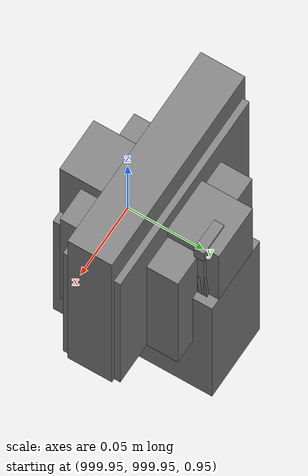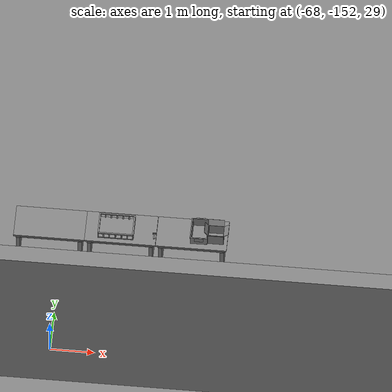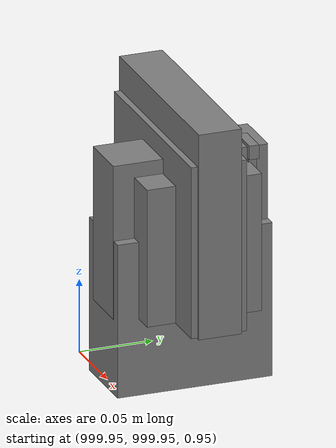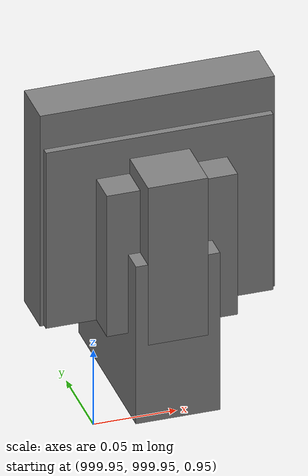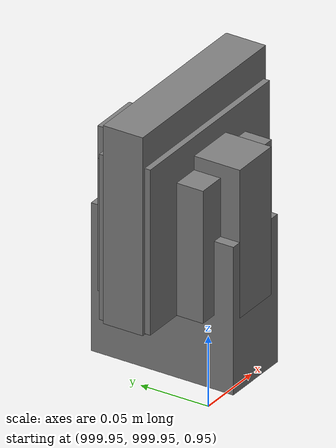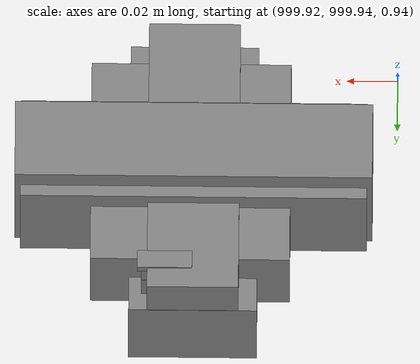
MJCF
<mujoco>
    <option gravity="0.000000000 0.000000000 -9.810000420" timestep="0.0049999999" integrator="implicitfast" density="1.225" viscosity="1.8000001e-05" noslip_iterations="10" iterations="100" sdf_iterations="50">
        <flag multiccd="disable"/>
    </option>
    <size memory="1000M"/>
    <compiler coordinate="local"/>
    <worldbody>
        <light cutoff="30" pos="0 1 1" dir="0 -1 -2"/>
        <light cutoff="30" pos="0 -1 1" dir="0 1 -2"/>
        <body pos="-66.276100159 -149.552505493 31.169155121" euler="-14.863959312 -71.329338074 -83.418472290" mocap="true" name="spotlight4_SpotLight"/>
        <body pos="1000.000000000 1000.000000000 1.000000000" euler="0.000000000 0.000000000 180.000000000" name="openloong_gripper_2f85_fix_base_usda_battery_01">
            <geom contype="1" conaffinity="1" density="1000" type="box" material="" rgba="0.500000000 0.500000000 0.500000000 1.000000000" solimp="0.899999976 0.949999988 0.001000000" friction="1.000000000 0.005000000 0.000100000" solref="0.020000000 1.000000000" margin="0" condim="3" group="0" pos="-0.011123657 -0.041940309 0.101691343" quat="1.000000000 0.000000000 0.000000000 0.000000000" size="0.010800000 0.003375000 0.004725000" name="openloong_gripper_2f85_fix_base_usda_geom_1F75E49E_3BFB_48DC_BEE1_0880FD42A4B8"/>
            <geom contype="1" conaffinity="1" density="1000" type="box" material="" rgba="0.500000000 0.500000000 0.500000000 1.000000000" solimp="0.899999976 0.949999988 0.001000000" friction="1.000000000 0.005000000 0.000100000" solref="0.020000000 1.000000000" margin="0" condim="3" group="0" pos="-0.010876465 -0.044247437 0.047066893" quat="0.998702705 -0.050920475 0.000000000 0.000000000" size="0.009450001 0.002700000 0.024975000" name="openloong_gripper_2f85_fix_base_usda_geom_A616A99B_CDCB_4701_AC16_2CD7D64A1FBD"/>
            <geom contype="1" conaffinity="1" density="1000" type="box" material="" rgba="0.500000000 0.500000000 0.500000000 1.000000000" solimp="0.899999976 0.949999988 0.001000000" friction="1.000000000 0.005000000 0.000100000" solref="0.020000000 1.000000000" margin="0" condim="3" group="0" pos="-0.001235962 -0.000659180 0.047381196" quat="1.000000000 0.000000000 0.000000000 0.000000000" size="0.039420001 0.039150000 0.047250003" name="openloong_gripper_2f85_fix_base_usda_geom_AA14815D_3656_4A3C_92E8_B350A3F5F55D"/>
            <geom contype="1" conaffinity="1" density="1000" type="box" material="" rgba="0.500000000 0.500000000 0.500000000 1.000000000" solimp="0.899999976 0.949999988 0.001000000" friction="1.000000000 0.005000000 0.000100000" solref="0.020000000 1.000000000" margin="0" condim="3" group="0" pos="-0.010876465 -0.039138794 0.009851727" quat="1.000000000 0.000000000 0.000000000 0.000000000" size="0.009450001 0.010800000 0.013500000" name="openloong_gripper_2f85_fix_base_usda_geom_F8617890_AC34_4167_A0CA_DAF78A078CA4"/>
            <geom contype="1" conaffinity="1" density="1000" type="box" material="" rgba="0.500000000 0.500000000 0.500000000 1.000000000" solimp="0.899999976 0.949999988 0.001000000" friction="1.000000000 0.005000000 0.000100000" solref="0.020000000 1.000000000" margin="0" condim="3" group="0" pos="-0.010876465 -0.041528322 0.071508206" quat="1.000000000 0.000000000 0.000000000 0.000000000" size="0.009450001 0.002700000 0.027000001" name="openloong_gripper_2f85_fix_base_usda_geom_DB7E06DB_DACD_499E_B6A0_57CBC2885AB4"/>
            <freejoint name="openloong_gripper_2f85_fix_base_usda_battery_01_joint"/>
            <site size="0.005000000 0.005000000 0.005000000" rgba="0.500000000 0.500000000 0.500000000 1.000000000" pos="0.000000000 0.000000000 0.000000000" quat="0.999961913 0.008726500 0.000000000 0.000000000" group="0" type="sphere" name="openloong_gripper_2f85_fix_base_usda_battery_01site"/>
        </body>
        <body pos="-66.192329407 -148.926788330 31.163356781" euler="-82.762641907 12.302098274 173.845169067" mocap="true" name="spotlight3_SpotLight"/>
        <body pos="1000.000000000 1000.000000000 1.000000000" euler="0.000000000 0.000000000 180.000000000" name="openloong_gripper_2f85_fix_base_usda_cpu_fan">
            <geom contype="1" conaffinity="1" density="1000" type="box" material="" rgba="0.500000000 0.500000000 0.500000000 1.000000000" solimp="0.899999976 0.949999988 0.001000000" friction="1.000000000 0.005000000 0.000100000" solref="0.020000000 1.000000000" margin="0" condim="3" group="0" pos="0.000000000 0.000000000 0.070034981" quat="0.000000000 0.000000000 0.000000000 1.000000000" size="0.070700005 0.014699999 0.070700005" name="openloong_gripper_2f85_fix_base_usda_geom_4D13E27C_841B_4E87_A3EF_FCD58CE6C8CC"/>
            <freejoint name="openloong_gripper_2f85_fix_base_usda_cpu_fan_joint"/>
            <site size="0.005000000 0.005000000 0.005000000" rgba="0.500000000 0.500000000 0.500000000 1.000000000" pos="0.000000000 0.000000000 0.000000000" quat="0.999961913 0.008726535 0.000000000 0.000000000" group="0" type="sphere" name="openloong_gripper_2f85_fix_base_usda_cpu_fancsite"/>
        </body>
        <body pos="1000.000000000 1000.000000000 1.000000000" euler="0.000000000 0.000000000 180.000000000" name="openloong_gripper_2f85_fix_base_usda_wifi_box">
            <geom contype="1" conaffinity="1" density="1000" type="box" material="" rgba="0.500000000 0.500000000 0.500000000 1.000000000" solimp="0.899999976 0.949999988 0.001000000" friction="1.000000000 0.005000000 0.000100000" solref="0.020000000 1.000000000" margin="0" condim="3" group="0" pos="0.000000000 0.000000000 0.058978677" quat="0.000000000 0.000000047 0.000000000 1.000000000" size="0.068499997 0.018999999 0.059000000" name="openloong_gripper_2f85_fix_base_usda_geom_FBB199E4_F51C_4ED0_A540_7D359D8DE13A"/>
            <freejoint name="openloong_gripper_2f85_fix_base_usda_wifi_box_joint"/>
            <site size="0.005000000 0.005000000 0.005000000" rgba="0.500000000 0.500000000 0.500000000 1.000000000" pos="0.000000000 0.000000000 0.000000000" quat="0.999961913 0.008726500 0.000000000 0.000000000" group="0" type="sphere" name="openloong_gripper_2f85_fix_base_usda_wifi_boxsite"/>
        </body>
        <body pos="1000.000000000 1000.000000000 1.000000000" euler="0.000011953 0.000005123 -179.999984741" name="openloong_gripper_2f85_fix_base_usda_intel_box">
            <geom contype="1" conaffinity="1" density="1000" type="box" material="" rgba="0.500000000 0.500000000 0.500000000 1.000000000" solimp="0.899999976 0.949999988 0.001000000" friction="1.000000000 0.005000000 0.000100000" solref="0.020000000 1.000000000" margin="0" condim="3" group="0" pos="0.000000000 -0.000067139 0.000082284" quat="0.707106709 0.000000225 0.000000253 0.707106650" size="0.052800003 0.025300000 0.052800003" name="openloong_gripper_2f85_fix_base_usda_geom_F483B1F9_7F55_4603_9FCB_09E68C862DBE"/>
            <freejoint name="openloong_gripper_2f85_fix_base_usda_intel_box_joint"/>
            <site size="0.005000000 0.005000000 0.005000000" rgba="0.500000000 0.500000000 0.500000000 1.000000000" pos="0.000000000 0.000000000 0.000000000" quat="0.999961913 0.008726500 0.000000000 0.000000000" group="0" type="sphere" name="openloong_gripper_2f85_fix_base_usda_intel_boxsite"/>
        </body>
        <body pos="1000.000000000 999.999938965 1.000000000" euler="0.000000000 0.000000000 180.000000000" name="openloong_gripper_2f85_fix_base_usda_intelcore_i5">
            <geom contype="1" conaffinity="1" density="1000" type="box" material="" rgba="0.500000000 0.500000000 0.500000000 1.000000000" solimp="0.899999976 0.949999988 0.001000000" friction="1.000000000 0.005000000 0.000100000" solref="0.020000000 1.000000000" margin="0" condim="3" group="0" pos="0.000000000 0.000000000 0.051722717" quat="0.707106709 0.000000000 0.000000000 -0.707106769" size="0.052800000 0.018080002 0.052800000" name="openloong_gripper_2f85_fix_base_usda_geom_BE2C70B2_C4C0_4755_B614_6F7008BC9C50"/>
            <freejoint name="openloong_gripper_2f85_fix_base_usda_intelcore_i5_joint"/>
            <site size="0.005000000 0.005000000 0.005000000" rgba="0.500000000 0.500000000 0.500000000 1.000000000" pos="0.000000000 0.000000000 0.000000000" quat="0.999961913 0.008726534 0.000000000 0.000000000" group="0" type="sphere" name="openloong_gripper_2f85_fix_base_usda_intelcore_i5site"/>
        </body>
        <body pos="-66.330688477 -149.265777588 31.169132233" euler="-4.702430248 16.492101669 152.228942871" mocap="true" name="spotlight1_SpotLight"/>
        <body pos="-64.866622925 -149.383972168 30.183746338" euler="89.999984741 89.999946594 0.000000000" name="openloong_gripper_2f85_fix_base_usda_bluebox_01">
            <geom contype="1" conaffinity="1" density="1000" type="box" material="" rgba="0.500000000 0.500000000 0.500000000 1.000000000" solimp="0.899999976 0.949999988 0.001000000" friction="1.000000000 0.005000000 0.000100000" solref="0.020000000 1.000000000" margin="0" condim="3" group="0" pos="0.276580811 0.187225342 0.000068665" quat="0.707106948 0.000077471 0.707106352 0.000077486" size="0.100000001 0.057999998 0.010000000" name="openloong_gripper_2f85_fix_base_usda_geom_971051F0_B9D7_42E3_9375_0B7B13B0F69E"/>
            <geom contype="1" conaffinity="1" density="1000" type="box" material="" rgba="0.500000000 0.500000000 0.500000000 1.000000000" solimp="0.899999976 0.949999988 0.001000000" friction="1.000000000 0.005000000 0.000100000" solref="0.020000000 1.000000000" margin="0" condim="3" group="0" pos="0.000000000 0.002883911 0.000000000" quat="0.999999881 0.000000000 0.000000000 0.000000000" size="0.254000008 0.003000000 0.172000006" name="openloong_gripper_2f85_fix_base_usda_geom_C4397B02_045D_4DE2_9012_265D3568C770"/>
            <geom contype="1" conaffinity="1" density="1000" type="box" material="" rgba="0.500000000 0.500000000 0.500000000 1.000000000" solimp="0.899999976 0.949999988 0.001000000" friction="1.000000000 0.005000000 0.000100000" solref="0.020000000 1.000000000" margin="0" condim="3" group="0" pos="0.000000000 0.124874115 0.173484802" quat="0.999796331 0.020176515 -0.000000015 0.000000030" size="0.259999990 0.119999997 0.007000000" name="openloong_gripper_2f85_fix_base_usda_geom_6816A8D5_8493_41DD_BAF3_816B76F6FEFC"/>
            <geom contype="1" conaffinity="1" density="1000" type="box" material="" rgba="0.500000000 0.500000000 0.500000000 1.000000000" solimp="0.899999976 0.949999988 0.001000000" friction="1.000000000 0.005000000 0.000100000" solref="0.020000000 1.000000000" margin="0" condim="3" group="0" pos="0.000000000 0.124874115 -0.173469543" quat="0.999796331 -0.020176545 -0.000000015 0.000000000" size="0.259999990 0.119999997 0.007000000" name="openloong_gripper_2f85_fix_base_usda_geom_A5C94D34_357A_42D5_AF3D_C2BCA2B6003E"/>
            <geom contype="1" conaffinity="1" density="1000" type="box" material="" rgba="0.500000000 0.500000000 0.500000000 1.000000000" solimp="0.899999976 0.949999988 0.001000000" friction="1.000000000 0.005000000 0.000100000" solref="0.020000000 1.000000000" margin="0" condim="3" group="0" pos="0.000000000 0.214008331 0.188980103" quat="0.999912977 0.013176724 0.000000015 0.000000000" size="0.259999990 0.029999999 0.012500000" name="openloong_gripper_2f85_fix_base_usda_geom_33E84969_A980_4941_8078_BDDB78F9124A"/>
            <geom contype="1" conaffinity="1" density="1000" type="box" material="" rgba="0.500000000 0.500000000 0.500000000 1.000000000" solimp="0.899999976 0.949999988 0.001000000" friction="1.000000000 0.005000000 0.000100000" solref="0.020000000 1.000000000" margin="0" condim="3" group="0" pos="-0.258361816 0.125289917 0.001876831" quat="0.702796936 -0.020792112 0.710783124 0.020769298" size="0.189999998 0.119999997 0.009000000" name="openloong_gripper_2f85_fix_base_usda_geom_93CA830D_D0C6_4AF3_B912_E4B7518E7AF5"/>
            <geom contype="1" conaffinity="1" density="1000" type="box" material="" rgba="0.500000000 0.500000000 0.500000000 1.000000000" solimp="0.899999976 0.949999988 0.001000000" friction="1.000000000 0.005000000 0.000100000" solref="0.020000000 1.000000000" margin="0" condim="3" group="0" pos="0.000000000 0.214008331 -0.188980103" quat="0.999912977 -0.013176769 0.000000030 0.000000015" size="0.259999990 0.029999999 0.012500000" name="openloong_gripper_2f85_fix_base_usda_geom_BB866148_3969_49CF_A0C4_56B582AAC362"/>
            <geom contype="1" conaffinity="1" density="1000" type="box" material="" rgba="0.500000000 0.500000000 0.500000000 1.000000000" solimp="0.899999976 0.949999988 0.001000000" friction="1.000000000 0.005000000 0.000100000" solref="0.020000000 1.000000000" margin="0" condim="3" group="0" pos="-0.276611328 0.187225342 0.000068665" quat="0.707106650 0.000077441 0.707106709 0.000077456" size="0.100000001 0.057999998 0.010000000" name="openloong_gripper_2f85_fix_base_usda_geom_57F54296_1463_4CDA_B0A9_2D9971459708"/>
            <geom contype="1" conaffinity="1" density="1000" type="box" material="" rgba="0.500000000 0.500000000 0.500000000 1.000000000" solimp="0.899999976 0.949999988 0.001000000" friction="1.000000000 0.005000000 0.000100000" solref="0.020000000 1.000000000" margin="0" condim="3" group="0" pos="0.258331299 0.125289917 0.001876831" quat="0.702851415 0.018856421 0.710823774 -0.019329369" size="0.189999998 0.119999997 0.009000000" name="openloong_gripper_2f85_fix_base_usda_geom_AC84D012_614F_431C_857E_2A636E3F02E1"/>
            <freejoint name="openloong_gripper_2f85_fix_base_usda_bluebox_01_joint"/>
            <site size="0.005000000 0.005000000 0.005000000" rgba="0.500000000 0.500000000 0.500000000 1.000000000" pos="0.000000000 0.000000000 0.000000000" quat="0.999961913 0.008726534 0.000000000 0.000000000" group="0" type="sphere" name="openloong_gripper_2f85_fix_base_usda_bluebox_01site"/>
        </body>
        <body pos="-64.496299744 -149.491867065 30.235729218" euler="0.000000000 0.000000000 89.999946594" name="openloong_gripper_2f85_fix_base_usda_cardboardbox_01">
            <geom contype="1" conaffinity="1" density="1000" type="box" material="" rgba="0.500000000 0.500000000 0.500000000 1.000000000" solimp="0.899999976 0.949999988 0.001000000" friction="1.000000000 0.005000000 0.000100000" solref="0.020000000 1.000000000" margin="0" condim="3" group="0" pos="-0.003166199 -0.004086494 0.005052090" quat="1.000000000 0.000000000 0.000000000 0.000000000" size="0.142499998 0.177500010 0.005000000" name="openloong_gripper_2f85_fix_base_usda_geom_DDCACB7D_2F17_44D4_8915_26690C1C684C"/>
            <geom contype="1" conaffinity="1" density="1000" type="box" material="" rgba="0.500000000 0.500000000 0.500000000 1.000000000" solimp="0.899999976 0.949999988 0.001000000" friction="1.000000000 0.005000000 0.000100000" solref="0.020000000 1.000000000" margin="0" condim="3" group="0" pos="-0.003166199 0.170316696 0.150570869" quat="1.000000000 0.000000000 0.000000000 0.000000000" size="0.142499998 0.005000000 0.149999991" name="openloong_gripper_2f85_fix_base_usda_geom_88796DBD_FE91_4844_BCF3_054CD22A3514"/>
            <geom contype="1" conaffinity="1" density="1000" type="box" material="" rgba="0.500000000 0.500000000 0.500000000 1.000000000" solimp="0.899999976 0.949999988 0.001000000" friction="1.000000000 0.005000000 0.000100000" solref="0.020000000 1.000000000" margin="0" condim="3" group="0" pos="-0.147399902 -0.005307198 0.150570869" quat="1.000000000 0.000000000 0.000000000 0.000000000" size="0.005000000 0.177500010 0.149999991" name="openloong_gripper_2f85_fix_base_usda_geom_03106926_F9BB_47D1_801B_4B9247117EF0"/>
            <geom contype="1" conaffinity="1" density="1000" type="box" material="" rgba="0.500000000 0.500000000 0.500000000 1.000000000" solimp="0.899999976 0.949999988 0.001000000" friction="1.000000000 0.005000000 0.000100000" solref="0.020000000 1.000000000" margin="0" condim="3" group="0" pos="0.140275955 -0.005307198 0.150570869" quat="1.000000000 0.000000000 0.000000000 0.000000000" size="0.005000000 0.177500010 0.149999991" name="openloong_gripper_2f85_fix_base_usda_geom_4CD62E43_9713_4987_BB24_51E406AED352"/>
            <geom contype="1" conaffinity="1" density="1000" type="box" material="" rgba="0.500000000 0.500000000 0.500000000 1.000000000" solimp="0.899999976 0.949999988 0.001000000" friction="1.000000000 0.005000000 0.000100000" solref="0.020000000 1.000000000" margin="0" condim="3" group="0" pos="-0.003166199 -0.181550980 0.150570869" quat="1.000000000 0.000000000 0.000000000 0.000000000" size="0.142499998 0.005000000 0.149999991" name="openloong_gripper_2f85_fix_base_usda_geom_3C27FA59_1AFF_4617_92EC_FBCD89C3B313"/>
            <freejoint name="openloong_gripper_2f85_fix_base_usda_cardboardbox_01_joint"/>
            <site size="0.005000000 0.005000000 0.005000000" rgba="0.500000000 0.500000000 0.500000000 1.000000000" pos="0.000000000 0.000000000 0.000000000" quat="0.999961913 0.008726535 0.000000000 0.000000000" group="0" type="sphere" name="openloong_gripper_2f85_fix_base_usda_site_9C7C8B35_F35B_4DE1_B78A_AA5E47B81095"/>
            <body pos="0.139160156 -0.004048347 0.301930904" euler="-179.999954224 49.383502960 179.999954224" name="openloong_gripper_2f85_fix_base_usda_A1_006">
                <geom contype="1" conaffinity="1" density="1000" type="box" material="" rgba="0.500000000 0.500000000 0.500000000 1.000000000" solimp="0.899999976 0.949999988 0.001000000" friction="1.000000000 0.005000000 0.000100000" solref="0.020000000 1.000000000" margin="0" condim="3" group="0" pos="-0.071587563 0.000009537 0.001745224" quat="0.999999881 0.000000000 0.000000000 0.000000000" size="0.071249999 0.179999992 0.002500000" name="openloong_gripper_2f85_fix_base_usda_geom_A7AC9CFA_A631_4517_AF4E_52A5D1E42FBE"/>
                <joint armature="0" stiffness="0.07" damping="0.0099999998" axis="0.000000 1.000000 0.000000" type="hinge" name="openloong_gripper_2f85_fix_base_usda_A1_006"/>
            </body>
            <body pos="-0.145902634 -0.004086494 0.301938057" euler="-180.000000000 -60.000011444 -180.000000000" name="openloong_gripper_2f85_fix_base_usda_A2_006">
                <geom contype="1" conaffinity="1" density="1000" type="box" material="" rgba="0.500000000 0.500000000 0.500000000 1.000000000" solimp="0.899999976 0.949999988 0.001000000" friction="1.000000000 0.005000000 0.000100000" solref="0.020000000 1.000000000" margin="0" condim="3" group="0" pos="0.071268082 0.000009537 0.002717972" quat="0.000002921 0.000000000 -0.000000030 0.999999881" size="0.071249999 0.179999992 0.002500000" name="openloong_gripper_2f85_fix_base_usda_geom_238378FF_9E1B_44CB_9F68_BBA767002391"/>
                <joint armature="0" stiffness="0.07" damping="0.0099999998" axis="0.000000 1.000000 0.000000" type="hinge" name="openloong_gripper_2f85_fix_base_usda_A2_006"/>
            </body>
            <body pos="-0.003385544 0.175991058 0.301930904" euler="-125.858116150 -0.000004561 0.000002331" name="openloong_gripper_2f85_fix_base_usda_B2_006">
                <geom contype="1" conaffinity="1" density="1000" type="box" material="" rgba="0.500000000 0.500000000 0.500000000 1.000000000" solimp="0.899999976 0.949999988 0.001000000" friction="1.000000000 0.005000000 0.000100000" solref="0.020000000 1.000000000" margin="0" condim="3" group="0" pos="0.000009537 -0.070939064 -0.002470016" quat="0.999614120 0.027776197 -0.000000015 0.000000030" size="0.137500003 0.064999998 0.005000000" name="openloong_gripper_2f85_fix_base_usda_geom_DADAB2D7_91C0_45D7_BB8C_0D548441F43E"/>
                <joint armature="0" stiffness="0.07" damping="0.0099999998" axis="1.000000 0.000000 0.000000" type="hinge" name="openloong_gripper_2f85_fix_base_usda_B2_006"/>
            </body>
            <body pos="-0.003385544 -0.184140205 0.301938057" euler="147.805557251 0.000000000 0.000000000" name="openloong_gripper_2f85_fix_base_usda_B1_006">
                <geom contype="1" conaffinity="1" density="1000" type="box" material="" rgba="0.500000000 0.500000000 0.500000000 1.000000000" solimp="0.899999976 0.949999988 0.001000000" friction="1.000000000 0.005000000 0.000100000" solref="0.020000000 1.000000000" margin="0" condim="3" group="0" pos="-0.000028610 0.070202351 -0.002703667" quat="0.999614179 -0.027776167 0.000000000 0.000000000" size="0.137500003 0.064999998 0.005000000" name="openloong_gripper_2f85_fix_base_usda_geom_96AD5BAE_6AA9_4D01_9374_031B120BCB77"/>
                <joint armature="0" stiffness="0.07" damping="0.0099999998" axis="1.000000 0.000000 0.000000" type="hinge" name="openloong_gripper_2f85_fix_base_usda_B1_006"/>
            </body>
        </body>
        <body pos="-65.882858276 -149.481979370 30.229999542" euler="-64.487716675 0.000000000 0.000000000" name="openloong_gripper_2f85_fix_base_usda_Barcode">
            <geom contype="1" conaffinity="1" density="1000" type="box" material="" rgba="0.500000000 0.500000000 0.500000000 1.000000000" solimp="0.899999976 0.949999988 0.001000000" friction="1.000000000 0.005000000 0.000100000" solref="0.020000000 1.000000000" margin="0" condim="3" group="0" pos="0.000000000 0.013038635 0.001419067" quat="0.000000000 0.000000000 0.000000000 1.000000119" size="0.034000002 0.010000000 0.017999999" name="openloong_gripper_2f85_fix_base_usda_geom_07C3B74B_E71C_4D2F_B7BD_5BEE1D6F16B3"/>
            <geom contype="1" conaffinity="1" density="1000" type="box" material="" rgba="0.500000000 0.500000000 0.500000000 1.000000000" solimp="0.899999976 0.949999988 0.001000000" friction="1.000000000 0.005000000 0.000100000" solref="0.020000000 1.000000000" margin="0" condim="3" group="0" pos="0.000000000 -0.035301208 -0.007095337" quat="0.000000000 0.000000000 -0.043619365 0.999048233" size="0.028999999 0.010000000 0.020000000" name="openloong_gripper_2f85_fix_base_usda_geom_CDB8E3BF_856D_489C_84FD_A27E83E931DB"/>
            <geom contype="1" conaffinity="1" density="1000" type="box" material="" rgba="0.500000000 0.500000000 0.500000000 1.000000000" solimp="0.899999976 0.949999988 0.001000000" friction="1.000000000 0.005000000 0.000100000" solref="0.020000000 1.000000000" margin="0" condim="3" group="0" pos="0.000000000 -0.043411255 -0.011749268" quat="0.922262907 0.386563420 0.000000000 0.000000000" size="0.026000001 0.010000000 0.020000000" name="openloong_gripper_2f85_fix_base_usda_geom_5127C08C_0B12_4C2A_9EE6_4CB5F8B73D51"/>
            <geom contype="1" conaffinity="1" density="1000" type="box" material="" rgba="0.500000000 0.500000000 0.500000000 1.000000000" solimp="0.899999976 0.949999988 0.001000000" friction="1.000000000 0.005000000 0.000100000" solref="0.020000000 1.000000000" margin="0" condim="3" group="0" pos="0.000000000 -0.016967773 -0.031860352" quat="0.000000000 0.000000000 0.000000000 1.000000119" size="0.008000000 0.010000000 0.013000000" name="openloong_gripper_2f85_fix_base_usda_geom_7BB2E0D2_807A_485A_9B8C_3392F08A2968"/>
            <geom contype="1" conaffinity="1" density="1000" type="box" material="" rgba="0.500000000 0.500000000 0.500000000 1.000000000" solimp="0.899999976 0.949999988 0.001000000" friction="1.000000000 0.005000000 0.000100000" solref="0.020000000 1.000000000" margin="0" condim="3" group="0" pos="0.000000000 -0.001869202 0.000312805" quat="0.953716993 0.300705761 0.000000000 0.000000000" size="0.032000002 0.010000000 0.018999999" name="openloong_gripper_2f85_fix_base_usda_geom_10568586_98A0_4905_B82C_328352D10126"/>
            <geom contype="1" conaffinity="1" density="1000" type="box" material="" rgba="0.500000000 0.500000000 0.500000000 1.000000000" solimp="0.899999976 0.949999988 0.001000000" friction="1.000000000 0.005000000 0.000100000" solref="0.020000000 1.000000000" margin="0" condim="3" group="0" pos="0.000000000 -0.019531250 -0.003173828" quat="0.953716993 0.300705761 0.000000000 0.000000000" size="0.030999999 0.010000000 0.020000000" name="openloong_gripper_2f85_fix_base_usda_geom_77339E75_0CC7_4E05_85FF_CDAFF5EE4D3E"/>
            <geom contype="1" conaffinity="1" density="1000" type="box" material="" rgba="0.500000000 0.500000000 0.500000000 1.000000000" solimp="0.899999976 0.949999988 0.001000000" friction="1.000000000 0.005000000 0.000100000" solref="0.020000000 1.000000000" margin="0" condim="3" group="0" pos="0.000000000 -0.035301208 -0.007095337" quat="0.953716993 0.300705761 0.000000000 0.000000000" size="0.028999999 0.010000000 0.020000000" name="openloong_gripper_2f85_fix_base_usda_geom_DD058C1A_89AA_483D_9260_DA86B6568F9A"/>
            <geom contype="1" conaffinity="1" density="1000" type="box" material="" rgba="0.500000000 0.500000000 0.500000000 1.000000000" solimp="0.899999976 0.949999988 0.001000000" friction="1.000000000 0.005000000 0.000100000" solref="0.020000000 1.000000000" margin="0" condim="3" group="0" pos="0.000000000 -0.042617798 -0.071121216" quat="0.000000000 0.000000000 0.000000000 1.000000119" size="0.013000000 0.021000000 0.059999999" name="openloong_gripper_2f85_fix_base_usda_geom_7E26EA95_B73F_4EFE_8E6A_047B4B07702A"/>
            <freejoint name="openloong_gripper_2f85_fix_base_usda_Barcode_joint"/>
            <site size="0.005000000 0.005000000 0.005000000" rgba="0.500000000 0.500000000 0.500000000 1.000000000" pos="0.000000000 0.000000000 0.000000000" quat="1.000000000 0.000000000 0.000000000 0.000000000" group="0" type="sphere" name="openloong_gripper_2f85_fix_base_usda_Barcode_site"/>
        </body>
        <body pos="-66.745018005 -149.392349243 30.184000015" euler="0.000000000 0.000000000 89.999946594" name="[22329739483693]_Basket_01">
            <geom contype="1" conaffinity="1" density="1000" type="box" material="" rgba="0.500000000 0.500000000 0.500000000 1.000000000" solimp="0.899999976 0.949999988 0.001000000" friction="1.000000000 0.005000000 0.000100000" solref="0.020000000 1.000000000" margin="0" condim="3" group="0" pos="-0.052425385 0.389207840 0.089787483" quat="0.707107008 0.000000000 0.000000000 0.707106411" size="0.014249999 0.014249999 0.059999999" name="[22329739483693]_geom_29291EB1_8B55_401F_8671_BD0EE205C606"/>
            <geom contype="1" conaffinity="1" density="1000" type="box" material="" rgba="0.500000000 0.500000000 0.500000000 1.000000000" solimp="0.899999976 0.949999988 0.001000000" friction="1.000000000 0.005000000 0.000100000" solref="0.020000000 1.000000000" margin="0" condim="3" group="0" pos="0.264015198 -0.133043289 0.089787483" quat="0.707107008 0.000000000 0.000000000 0.707106411" size="0.014249999 0.014249999 0.059999999" name="[22329739483693]_geom_13498506_8A44_4327_B6FD_27DC092D686F"/>
            <geom contype="1" conaffinity="1" density="1000" type="box" material="" rgba="0.500000000 0.500000000 0.500000000 1.000000000" solimp="0.899999976 0.949999988 0.001000000" friction="1.000000000 0.005000000 0.000100000" solref="0.020000000 1.000000000" margin="0" condim="3" group="0" pos="-0.264015198 -0.265548706 0.089793205" quat="0.707107008 0.000000000 0.000000000 0.707106411" size="0.014249999 0.014249999 0.059999999" name="[22329739483693]_geom_F667BF24_247D_4B13_BA5A_81EB2EA216BC"/>
            <geom contype="1" conaffinity="1" density="1000" type="box" material="" rgba="0.500000000 0.500000000 0.500000000 1.000000000" solimp="0.899999976 0.949999988 0.001000000" friction="1.000000000 0.005000000 0.000100000" solref="0.020000000 1.000000000" margin="0" condim="3" group="0" pos="-0.160263062 -0.389322281 0.089793205" quat="0.707107008 0.000000000 0.000000000 0.707106411" size="0.014249999 0.014249999 0.059999999" name="[22329739483693]_geom_FE93484C_A9A2_468E_A423_384747D3A65D"/>
            <geom contype="1" conaffinity="1" density="1000" type="box" material="" rgba="0.500000000 0.500000000 0.500000000 1.000000000" solimp="0.899999976 0.949999988 0.001000000" friction="1.000000000 0.005000000 0.000100000" solref="0.020000000 1.000000000" margin="0" condim="3" group="0" pos="0.162265778 -0.389322281 0.089787483" quat="0.707107008 0.000000000 0.000000000 0.707106411" size="0.014249999 0.014249999 0.059999999" name="[22329739483693]_geom_407A36C1_CC0C_4E67_A123_2E5102AC5C99"/>
            <geom contype="1" conaffinity="1" density="1000" type="box" material="" rgba="0.500000000 0.500000000 0.500000000 1.000000000" solimp="0.899999976 0.949999988 0.001000000" friction="1.000000000 0.005000000 0.000100000" solref="0.020000000 1.000000000" margin="0" condim="3" group="0" pos="0.264015198 0.389207840 0.089787483" quat="0.707107008 0.000000000 0.000000000 0.707106411" size="0.014249999 0.014249999 0.059999999" name="[22329739483693]_geom_34FC48E3_DF49_41CB_B703_5C7D6CE9F8FD"/>
            <geom contype="1" conaffinity="1" density="1000" type="box" material="" rgba="0.500000000 0.500000000 0.500000000 1.000000000" solimp="0.899999976 0.949999988 0.001000000" friction="1.000000000 0.005000000 0.000100000" solref="0.020000000 1.000000000" margin="0" condim="3" group="0" pos="-0.264015198 -0.133043289 0.089793205" quat="0.707107008 0.000000000 0.000000000 0.707106411" size="0.014249999 0.014249999 0.059999999" name="[22329739483693]_geom_8631A3D1_573A_4D29_B2FB_52BEE6741914"/>
            <geom contype="1" conaffinity="1" density="1000" type="box" material="" rgba="0.500000000 0.500000000 0.500000000 1.000000000" solimp="0.899999976 0.949999988 0.001000000" friction="1.000000000 0.005000000 0.000100000" solref="0.020000000 1.000000000" margin="0" condim="3" group="0" pos="-0.264026642 0.269256592 0.089793205" quat="0.707107008 0.000000000 0.000000000 0.707106411" size="0.014249999 0.014249999 0.059999999" name="[22329739483693]_geom_658E73EF_1EAA_48BB_B714_5583C6E926C8"/>
            <geom contype="1" conaffinity="1" density="1000" type="box" material="" rgba="0.500000000 0.500000000 0.500000000 1.000000000" solimp="0.899999976 0.949999988 0.001000000" friction="1.000000000 0.005000000 0.000100000" solref="0.020000000 1.000000000" margin="0" condim="3" group="0" pos="0.054462433 0.389207840 0.089787483" quat="0.707107008 0.000000000 0.000000000 0.707106411" size="0.014249999 0.014249999 0.059999999" name="[22329739483693]_geom_28E7855D_D6FF_4052_9944_69EB9C45CB4E"/>
            <geom contype="1" conaffinity="1" density="1000" type="box" material="" rgba="0.500000000 0.500000000 0.500000000 1.000000000" solimp="0.899999976 0.949999988 0.001000000" friction="1.000000000 0.005000000 0.000100000" solref="0.020000000 1.000000000" margin="0" condim="3" group="0" pos="0.054462433 -0.389322281 0.089787483" quat="0.707107008 0.000000000 0.000000000 0.707106411" size="0.014249999 0.014249999 0.059999999" name="[22329739483693]_geom_30533BDB_0553_4B51_B04A_83B476D5BA78"/>
            <geom contype="1" conaffinity="1" density="1000" type="box" material="" rgba="0.500000000 0.500000000 0.500000000 1.000000000" solimp="0.899999976 0.949999988 0.001000000" friction="1.000000000 0.005000000 0.000100000" solref="0.020000000 1.000000000" margin="0" condim="3" group="0" pos="0.264015198 0.269256592 0.089793205" quat="0.707107008 0.000000000 0.000000000 0.707106411" size="0.014249999 0.014249999 0.059999999" name="[22329739483693]_geom_99E63A0C_86FA_4703_8575_CB882E292D90"/>
            <geom contype="1" conaffinity="1" density="1000" type="box" material="" rgba="0.500000000 0.500000000 0.500000000 1.000000000" solimp="0.899999976 0.949999988 0.001000000" friction="1.000000000 0.005000000 0.000100000" solref="0.020000000 1.000000000" margin="0" condim="3" group="0" pos="0.264015198 -0.389322281 0.089787483" quat="0.707107008 0.000000000 0.000000000 0.707106411" size="0.014249999 0.014249999 0.059999999" name="[22329739483693]_geom_EC7CA510_5F89_4C97_9E33_2A100364A15A"/>
            <geom contype="1" conaffinity="1" density="1000" type="box" material="" rgba="0.500000000 0.500000000 0.500000000 1.000000000" solimp="0.899999976 0.949999988 0.001000000" friction="1.000000000 0.005000000 0.000100000" solref="0.020000000 1.000000000" margin="0" condim="3" group="0" pos="0.000000000 0.000000000 0.015998840" quat="0.707107008 0.000000000 0.000000000 0.707106411" size="0.403499991 0.279000014 0.015750000" name="[22329739483693]_geom_6AB7DBFF_ECEF_4892_ABB0_26836A468023"/>
            <geom contype="1" conaffinity="1" density="1000" type="box" material="" rgba="0.500000000 0.500000000 0.500000000 1.000000000" solimp="0.899999976 0.949999988 0.001000000" friction="1.000000000 0.005000000 0.000100000" solref="0.020000000 1.000000000" margin="0" condim="3" group="0" pos="0.000000000 -0.389476776 0.163619041" quat="0.707107008 0.000000000 0.000000000 0.707106411" size="0.015000000 0.277500004 0.015750000" name="[22329739483693]_geom_E6133910_C4C6_4925_AA76_7A36CAC998A2"/>
            <geom contype="1" conaffinity="1" density="1000" type="box" material="" rgba="0.500000000 0.500000000 0.500000000 1.000000000" solimp="0.899999976 0.949999988 0.001000000" friction="1.000000000 0.005000000 0.000100000" solref="0.020000000 1.000000000" margin="0" condim="3" group="0" pos="0.162265778 0.389207840 0.089787483" quat="0.707107008 0.000000000 0.000000000 0.707106411" size="0.014249999 0.014249999 0.059999999" name="[22329739483693]_geom_CC379663_545D_4F44_AF43_B488C17B6A7C"/>
            <geom contype="1" conaffinity="1" density="1000" type="box" material="" rgba="0.500000000 0.500000000 0.500000000 1.000000000" solimp="0.899999976 0.949999988 0.001000000" friction="1.000000000 0.005000000 0.000100000" solref="0.020000000 1.000000000" margin="0" condim="3" group="0" pos="0.000000000 0.389471054 0.163619041" quat="0.707107008 0.000000000 0.000000000 0.707106411" size="0.015000000 0.277500004 0.015750000" name="[22329739483693]_geom_7F08F8B4_BB95_4B1E_83EA_A76DEF25EDE6"/>
            <geom contype="1" conaffinity="1" density="1000" type="box" material="" rgba="0.500000000 0.500000000 0.500000000 1.000000000" solimp="0.899999976 0.949999988 0.001000000" friction="1.000000000 0.005000000 0.000100000" solref="0.020000000 1.000000000" margin="0" condim="3" group="0" pos="-0.263511658 0.000000000 0.163619041" quat="0.707107008 0.000000000 0.000000000 0.707106411" size="0.403499991 0.015000000 0.015750000" name="[22329739483693]_geom_4846E285_0198_478E_8CF4_E027F4561534"/>
            <geom contype="1" conaffinity="1" density="1000" type="box" material="" rgba="0.500000000 0.500000000 0.500000000 1.000000000" solimp="0.899999976 0.949999988 0.001000000" friction="1.000000000 0.005000000 0.000100000" solref="0.020000000 1.000000000" margin="0" condim="3" group="0" pos="-0.264015198 0.141334534 0.089793205" quat="0.707107008 0.000000000 0.000000000 0.707106411" size="0.014249999 0.014249999 0.059999999" name="[22329739483693]_geom_84AC5269_8DEC_441C_BD2F_3D9A55648D34"/>
            <geom contype="1" conaffinity="1" density="1000" type="box" material="" rgba="0.500000000 0.500000000 0.500000000 1.000000000" solimp="0.899999976 0.949999988 0.001000000" friction="1.000000000 0.005000000 0.000100000" solref="0.020000000 1.000000000" margin="0" condim="3" group="0" pos="0.264015198 -0.265548706 0.089787483" quat="0.707107008 0.000000000 0.000000000 0.707106411" size="0.014249999 0.014249999 0.059999999" name="[22329739483693]_geom_9660D607_107A_45F6_9121_D81902A7FBD9"/>
            <geom contype="1" conaffinity="1" density="1000" type="box" material="" rgba="0.500000000 0.500000000 0.500000000 1.000000000" solimp="0.899999976 0.949999988 0.001000000" friction="1.000000000 0.005000000 0.000100000" solref="0.020000000 1.000000000" margin="0" condim="3" group="0" pos="-0.160263062 0.389207840 0.089787483" quat="0.707107008 0.000000000 0.000000000 0.707106411" size="0.014249999 0.014249999 0.059999999" name="[22329739483693]_geom_DE2C43EB_B94A_4980_BEF6_989E84DED839"/>
            <geom contype="1" conaffinity="1" density="1000" type="box" material="" rgba="0.500000000 0.500000000 0.500000000 1.000000000" solimp="0.899999976 0.949999988 0.001000000" friction="1.000000000 0.005000000 0.000100000" solref="0.020000000 1.000000000" margin="0" condim="3" group="0" pos="-0.052425385 -0.389322281 0.089787483" quat="0.707107008 0.000000000 0.000000000 0.707106411" size="0.014249999 0.014249999 0.059999999" name="[22329739483693]_geom_1BCA24A2_CA0E_4433_8841_F6DAE2541002"/>
            <geom contype="1" conaffinity="1" density="1000" type="box" material="" rgba="0.500000000 0.500000000 0.500000000 1.000000000" solimp="0.899999976 0.949999988 0.001000000" friction="1.000000000 0.005000000 0.000100000" solref="0.020000000 1.000000000" margin="0" condim="3" group="0" pos="-0.264026642 -0.389322281 0.089793205" quat="0.707107008 0.000000000 0.000000000 0.707106411" size="0.014249999 0.014249999 0.059999999" name="[22329739483693]_geom_FD371EE4_4DE6_461D_A349_E05CEC8E6D81"/>
            <geom contype="1" conaffinity="1" density="1000" type="box" material="" rgba="0.500000000 0.500000000 0.500000000 1.000000000" solimp="0.899999976 0.949999988 0.001000000" friction="1.000000000 0.005000000 0.000100000" solref="0.020000000 1.000000000" margin="0" condim="3" group="0" pos="0.264015198 0.141334534 0.089787483" quat="0.707107008 0.000000000 0.000000000 0.707106411" size="0.014249999 0.014249999 0.059999999" name="[22329739483693]_geom_FDEEAB85_F4DE_495C_8A13_0CA53A3D3FFA"/>
            <geom contype="1" conaffinity="1" density="1000" type="box" material="" rgba="0.500000000 0.500000000 0.500000000 1.000000000" solimp="0.899999976 0.949999988 0.001000000" friction="1.000000000 0.005000000 0.000100000" solref="0.020000000 1.000000000" margin="0" condim="3" group="0" pos="-0.264015198 0.389207840 0.089793205" quat="0.707107008 0.000000000 0.000000000 0.707106411" size="0.014249999 0.014249999 0.059999999" name="[22329739483693]_geom_A04FF46D_1581_4EC4_A80C_E096EAAD4FD1"/>
            <geom contype="1" conaffinity="1" density="1000" type="box" material="" rgba="0.500000000 0.500000000 0.500000000 1.000000000" solimp="0.899999976 0.949999988 0.001000000" friction="1.000000000 0.005000000 0.000100000" solref="0.020000000 1.000000000" margin="0" condim="3" group="0" pos="0.264015198 0.004480362 0.089787483" quat="0.707107008 0.000000000 0.000000000 0.707106411" size="0.014249999 0.014249999 0.059999999" name="[22329739483693]_geom_3000407F_E1E9_4093_9825_975C89B67793"/>
            <geom contype="1" conaffinity="1" density="1000" type="box" material="" rgba="0.500000000 0.500000000 0.500000000 1.000000000" solimp="0.899999976 0.949999988 0.001000000" friction="1.000000000 0.005000000 0.000100000" solref="0.020000000 1.000000000" margin="0" condim="3" group="0" pos="0.263694763 -0.000011444 0.163619041" quat="0.707107008 0.000000000 0.000000000 0.707106411" size="0.403499991 0.015000000 0.015750000" name="[22329739483693]_geom_2FAD4A2A_434E_4452_948C_1940B653DF31"/>
            <geom contype="1" conaffinity="1" density="1000" type="box" material="" rgba="0.500000000 0.500000000 0.500000000 1.000000000" solimp="0.899999976 0.949999988 0.001000000" friction="1.000000000 0.005000000 0.000100000" solref="0.020000000 1.000000000" margin="0" condim="3" group="0" pos="-0.264015198 0.004480362 0.089793205" quat="0.707107008 0.000000000 0.000000000 0.707106411" size="0.014249999 0.014249999 0.059999999" name="[22329739483693]_geom_29582A19_8BE2_41F2_A6A9_C056D3692984"/>
            <freejoint name="[22329739483693]_joint_313923FC_46AF_44CD_A215_109597E2E553"/>
        </body>
        <body pos="0.000000000 0.000000000 0.000000000" euler="0.000000000 0.000000000 0.000000000" name="Static Objects_Static Objects">
            <geom contype="1" conaffinity="1" density="1000" type="box" material="" rgba="0.500000000 0.500000000 0.500000000 1.000000000" solimp="0.899999976 0.949999988 0.001000000" friction="1.000000000 0.005000000 0.000100000" solref="0.020000000 1.000000000" margin="0" condim="3" group="0" pos="-67.544113159 -149.365814209 29.727830887" quat="0.500000417 0.499999970 0.499999553 0.499999970" size="0.381000012 0.319999993 0.041000001" name="Static Objects_geom_9F3EACDA_F9E5_436A_9B4B_0FB5AF74F38F"/>
            <geom contype="1" conaffinity="1" density="1000" type="box" material="" rgba="0.500000000 0.500000000 0.500000000 1.000000000" solimp="0.899999976 0.949999988 0.001000000" friction="1.000000000 0.005000000 0.000100000" solref="0.020000000 1.000000000" margin="0" condim="3" group="0" pos="-68.239501953 -149.365814209 30.086868286" quat="0.500000417 0.499999970 0.499999553 0.499999970" size="0.370999992 0.039500002 0.745000005" name="Static Objects_geom_C3AA9A73_912A_4E07_81CA_CF41DC82D75F"/>
            <geom contype="1" conaffinity="1" density="1000" type="box" material="" rgba="0.500000000 0.500000000 0.500000000 1.000000000" solimp="0.899999976 0.949999988 0.001000000" friction="1.000000000 0.005000000 0.000100000" solref="0.020000000 1.000000000" margin="0" condim="3" group="0" pos="-68.239501953 -149.365814209 30.147235870" quat="0.500000417 0.499999970 0.499999553 0.499999970" size="0.400000006 0.022000000 0.800000012" name="Static Objects_geom_5911E5C0_39D0_438F_A70B_35FE21EA7A8E"/>
            <geom contype="1" conaffinity="1" density="1000" type="box" material="" rgba="0.500000000 0.500000000 0.500000000 1.000000000" solimp="0.899999976 0.949999988 0.001000000" friction="1.000000000 0.005000000 0.000100000" solref="0.020000000 1.000000000" margin="0" condim="3" group="0" pos="-68.934890747 -149.365814209 29.727830887" quat="0.500000417 0.499999970 0.499999553 0.499999970" size="0.381000012 0.319999993 0.041000001" name="Static Objects_geom_0B527DE6_9351_44EF_ABF6_7F22FDBABE83"/>
            <geom contype="1" conaffinity="1" density="1000" type="box" material="" rgba="0.500000000 0.500000000 0.500000000 1.000000000" solimp="0.899999976 0.949999988 0.001000000" friction="1.000000000 0.005000000 0.000100000" solref="0.020000000 1.000000000" margin="0" condim="3" group="0" pos="-68.239501953 -149.365814209 29.561563492" quat="0.500000417 0.499999970 0.499999553 0.499999970" size="0.020000000 0.022000000 0.660000026" name="Static Objects_geom_1D19B1D8_6550_4316_8324_CC1523033D32"/>
            <geom contype="1" conaffinity="1" density="1000" type="box" material="" rgba="0.500000000 0.500000000 0.500000000 1.000000000" solimp="0.899999976 0.949999988 0.001000000" friction="1.000000000 0.005000000 0.000100000" solref="0.020000000 1.000000000" margin="0" condim="3" group="0" pos="-65.945671082 -149.365814209 29.727830887" quat="0.500000417 0.499999970 0.499999553 0.499999970" size="0.381000012 0.319999993 0.041000001" name="Static Objects_geom_E862422E_F031_4BC4_94DB_3C4C8DCEBA9F"/>
            <geom contype="1" conaffinity="1" density="1000" type="box" material="" rgba="0.500000000 0.500000000 0.500000000 1.000000000" solimp="0.899999976 0.949999988 0.001000000" friction="1.000000000 0.005000000 0.000100000" solref="0.020000000 1.000000000" margin="0" condim="3" group="0" pos="-66.641059875 -149.365814209 30.086868286" quat="0.500000417 0.499999970 0.499999553 0.499999970" size="0.370999992 0.039500002 0.745000005" name="Static Objects_geom_F165171D_1AAF_4FD2_8AE0_63A231464472"/>
            <geom contype="1" conaffinity="1" density="1000" type="box" material="" rgba="0.500000000 0.500000000 0.500000000 1.000000000" solimp="0.899999976 0.949999988 0.001000000" friction="1.000000000 0.005000000 0.000100000" solref="0.020000000 1.000000000" margin="0" condim="3" group="0" pos="-66.641059875 -149.365814209 30.147235870" quat="0.500000417 0.499999970 0.499999553 0.499999970" size="0.400000006 0.022000000 0.800000012" name="Static Objects_geom_DE502BAE_FA1A_4C61_8083_A25C88D9327F"/>
            <geom contype="1" conaffinity="1" density="1000" type="box" material="" rgba="0.500000000 0.500000000 0.500000000 1.000000000" solimp="0.899999976 0.949999988 0.001000000" friction="1.000000000 0.005000000 0.000100000" solref="0.020000000 1.000000000" margin="0" condim="3" group="0" pos="-67.336448669 -149.365814209 29.727830887" quat="0.500000417 0.499999970 0.499999553 0.499999970" size="0.381000012 0.319999993 0.041000001" name="Static Objects_geom_B4BF8E89_1D2A_4F7F_A0CB_F886B0622A22"/>
            <geom contype="1" conaffinity="1" density="1000" type="box" material="" rgba="0.500000000 0.500000000 0.500000000 1.000000000" solimp="0.899999976 0.949999988 0.001000000" friction="1.000000000 0.005000000 0.000100000" solref="0.020000000 1.000000000" margin="0" condim="3" group="0" pos="-66.641059875 -149.365814209 29.561563492" quat="0.500000417 0.499999970 0.499999553 0.499999970" size="0.020000000 0.022000000 0.660000026" name="Static Objects_geom_54BE61DB_3537_49C7_8D6C_3747C6C01AA1"/>
            <geom contype="1" conaffinity="1" density="1000" type="box" material="" rgba="0.500000000 0.500000000 0.500000000 1.000000000" solimp="0.899999976 0.949999988 0.001000000" friction="1.000000000 0.005000000 0.000100000" solref="0.020000000 1.000000000" margin="0" condim="3" group="0" pos="-64.338577271 -149.365814209 29.727830887" quat="0.500000417 0.499999970 0.499999553 0.499999970" size="0.381000012 0.319999993 0.041000001" name="Static Objects_geom_288BC705_7AFB_4523_B101_C1FE28030D45"/>
            <geom contype="1" conaffinity="1" density="1000" type="box" material="" rgba="0.500000000 0.500000000 0.500000000 1.000000000" solimp="0.899999976 0.949999988 0.001000000" friction="1.000000000 0.005000000 0.000100000" solref="0.020000000 1.000000000" margin="0" condim="3" group="0" pos="-65.033966064 -149.365814209 30.086868286" quat="0.500000417 0.499999970 0.499999553 0.499999970" size="0.370999992 0.039500002 0.745000005" name="Static Objects_geom_8456300A_A343_4577_B16E_19AAB051DD15"/>
            <geom contype="1" conaffinity="1" density="1000" type="box" material="" rgba="0.500000000 0.500000000 0.500000000 1.000000000" solimp="0.899999976 0.949999988 0.001000000" friction="1.000000000 0.005000000 0.000100000" solref="0.020000000 1.000000000" margin="0" condim="3" group="0" pos="-65.033966064 -149.365814209 30.147235870" quat="0.500000417 0.499999970 0.499999553 0.499999970" size="0.400000006 0.022000000 0.800000012" name="Static Objects_geom_49C1D07E_AB32_44FB_88E1_78CB914A251E"/>
            <geom contype="1" conaffinity="1" density="1000" type="box" material="" rgba="0.500000000 0.500000000 0.500000000 1.000000000" solimp="0.899999976 0.949999988 0.001000000" friction="1.000000000 0.005000000 0.000100000" solref="0.020000000 1.000000000" margin="0" condim="3" group="0" pos="-65.729354858 -149.365814209 29.727830887" quat="0.500000417 0.499999970 0.499999553 0.499999970" size="0.381000012 0.319999993 0.041000001" name="Static Objects_geom_0DA37739_5A7B_46FB_A792_8A72323F9FB9"/>
            <geom contype="1" conaffinity="1" density="1000" type="box" material="" rgba="0.500000000 0.500000000 0.500000000 1.000000000" solimp="0.899999976 0.949999988 0.001000000" friction="1.000000000 0.005000000 0.000100000" solref="0.020000000 1.000000000" margin="0" condim="3" group="0" pos="-65.033966064 -149.365814209 29.561563492" quat="0.500000417 0.499999970 0.499999553 0.499999970" size="0.020000000 0.022000000 0.660000026" name="Static Objects_geom_4FA61992_8251_476B_933D_1D2944FEDA11"/>
            <geom contype="1" conaffinity="1" density="1000" type="box" material="" rgba="0.500000000 0.500000000 0.500000000 1.000000000" solimp="0.899999976 0.949999988 0.001000000" friction="1.000000000 0.005000000 0.000100000" solref="0.020000000 1.000000000" margin="0" condim="3" group="0" pos="-61.754566193 -137.853729248 33.906845093" quat="0.707107067 0.000000000 0.000000000 0.707106471" size="0.759999990 0.759999990 4.500000000" name="Static Objects_geom_B12C0D75_020E_47AC_A59C_7E0C0334E2B5"/>
            <geom contype="1" conaffinity="1" density="1000" type="box" material="" rgba="0.500000000 0.500000000 0.500000000 1.000000000" solimp="0.899999976 0.949999988 0.001000000" friction="1.000000000 0.005000000 0.000100000" solref="0.020000000 1.000000000" margin="0" condim="3" group="0" pos="-57.511135101 -144.927108765 31.707921982" quat="1.000000000 0.000000000 0.000000000 0.000000000" size="0.200000003 8.000000000 2.299999952" name="Static Objects_geom_12D3603C_08CD_443E_B762_81DD4E4E8F5D"/>
            <geom contype="1" conaffinity="1" density="1000" type="box" material="" rgba="0.500000000 0.500000000 0.500000000 1.000000000" solimp="0.899999976 0.949999988 0.001000000" friction="1.000000000 0.005000000 0.000100000" solref="0.020000000 1.000000000" margin="0" condim="3" group="0" pos="-80.517646790 -157.574050903 31.688196182" quat="0.707107067 0.000000000 0.000000000 0.707106471" size="0.600000024 0.600000024 2.299999952" name="Static Objects_geom_CEC45D6A_96F5_4CC5_961B_6742C6B572B4"/>
            <geom contype="1" conaffinity="1" density="1000" type="box" material="" rgba="0.500000000 0.500000000 0.500000000 1.000000000" solimp="0.899999976 0.949999988 0.001000000" friction="1.000000000 0.005000000 0.000100000" solref="0.020000000 1.000000000" margin="0" condim="3" group="0" pos="-80.711044312 -147.414932251 31.666158676" quat="1.000000000 0.000000000 0.000000000 0.000000000" size="0.200000003 10.000000000 2.299999952" name="Static Objects_geom_2BD22203_36B7_476E_A739_421241D5204A"/>
            <geom contype="1" conaffinity="1" density="1000" type="box" material="" rgba="0.500000000 0.500000000 0.500000000 1.000000000" solimp="0.899999976 0.949999988 0.001000000" friction="1.000000000 0.005000000 0.000100000" solref="0.020000000 1.000000000" margin="0" condim="3" group="0" pos="-57.687217712 -137.434692383 31.688196182" quat="0.707107067 0.000000000 0.000000000 0.707106471" size="0.600000024 0.600000024 2.299999952" name="Static Objects_geom_A7DC7C99_F3E6_4743_8046_BA9F2418A9B2"/>
            <geom contype="1" conaffinity="1" density="1000" type="box" material="" rgba="0.500000000 0.500000000 0.500000000 1.000000000" solimp="0.899999976 0.949999988 0.001000000" friction="1.000000000 0.005000000 0.000100000" solref="0.020000000 1.000000000" margin="0" condim="3" group="0" pos="-69.537033081 -140.263229370 31.714921951" quat="0.707107067 0.000000000 0.000000000 0.707106471" size="0.759999990 4.500000000 2.299999952" name="Static Objects_geom_F73AF30C_CFA4_41E7_A5DE_5B1C904DC186"/>
            <geom contype="1" conaffinity="1" density="1000" type="box" material="" rgba="0.500000000 0.500000000 0.500000000 1.000000000" solimp="0.899999976 0.949999988 0.001000000" friction="1.000000000 0.005000000 0.000100000" solref="0.020000000 1.000000000" margin="0" condim="3" group="0" pos="-80.073638916 -137.853713989 33.906845093" quat="0.707107067 0.000000000 0.000000000 0.707106471" size="0.759999990 0.759999990 4.500000000" name="Static Objects_geom_E43A06FB_97A2_400E_89F9_4A0202F29595"/>
            <geom contype="1" conaffinity="1" density="1000" type="box" material="" rgba="0.500000000 0.500000000 0.500000000 1.000000000" solimp="0.899999976 0.949999988 0.001000000" friction="1.000000000 0.005000000 0.000100000" solref="0.020000000 1.000000000" margin="0" condim="3" group="0" pos="-73.406707764 -155.734664917 31.707921982" quat="1.000000000 0.000000000 0.000000000 0.000000000" size="0.200000003 3.000000000 2.299999952" name="Static Objects_geom_8638AEAD_52D4_4E42_B59F_40B3A22E8F97"/>
            <geom contype="1" conaffinity="1" density="1000" type="box" material="" rgba="0.500000000 0.500000000 0.500000000 1.000000000" solimp="0.899999976 0.949999988 0.001000000" friction="1.000000000 0.005000000 0.000100000" solref="0.020000000 1.000000000" margin="0" condim="3" group="0" pos="-68.497543335 -137.448257446 31.707921982" quat="0.707107067 0.000000000 0.000000000 0.707106471" size="0.200000003 14.000000000 2.299999952" name="Static Objects_geom_FD2F9F03_F0B2_4214_BE70_9ABB6ED2C2FD"/>
            <geom contype="1" conaffinity="1" density="1000" type="cylinder" material="" rgba="0.500000000 0.500000000 0.500000000 1.000000000" solimp="0.899999976 0.949999988 0.001000000" friction="1.000000000 0.005000000 0.000100000" solref="0.020000000 1.000000000" margin="0" condim="3" group="0" pos="-68.868522644 -142.134506226 31.711090088" quat="0.707107067 0.000000000 0.000000000 0.707106471" size="0.509999990 2.299999952 1.000000000" name="Static Objects_geom_9D71CFEC_9DF2_4DA0_95F8_055EF48D8A99"/>
            <geom contype="1" conaffinity="1" density="1000" type="plane" material="" rgba="0.500000000 0.500000000 0.500000000 1.000000000" solimp="0.899999976 0.949999988 0.001000000" friction="1.000000000 0.005000000 0.000100000" solref="0.020000000 1.000000000" margin="0" condim="3" group="0" pos="-72.873703003 -147.131927490 29.409669876" quat="1.000000000 0.000000000 0.000000000 0.000000000" size="18.000000000 14.000000000 1.000000000" name="Static Objects_geom_6C1F5B6A_4432_40AC_8EEB_E70501AA1003"/>
            <geom contype="1" conaffinity="1" density="1000" type="box" material="" rgba="0.500000000 0.500000000 0.500000000 1.000000000" solimp="0.899999976 0.949999988 0.001000000" friction="1.000000000 0.005000000 0.000100000" solref="0.020000000 1.000000000" margin="0" condim="3" group="0" pos="-79.943580627 -157.782272339 31.707921982" quat="0.707107067 0.000000000 0.000000000 0.707106471" size="0.200000003 7.000000000 2.299999952" name="Static Objects_geom_C2ACB1A7_5381_4AE8_958D_F520A65A9995"/>
            <geom contype="1" conaffinity="1" density="1000" type="box" material="" rgba="0.500000000 0.500000000 0.500000000 1.000000000" solimp="0.899999976 0.949999988 0.001000000" friction="1.000000000 0.005000000 0.000100000" solref="0.020000000 1.000000000" margin="0" condim="3" group="0" pos="-65.421028137 -152.903442383 31.707921982" quat="0.707107067 0.000000000 0.000000000 0.707106471" size="0.200000003 7.800000191 2.299999952" name="Static Objects_geom_0F6BA45C_03FF_4EFC_9007_05FB59D3FCD8"/>
            <geom contype="1" conaffinity="1" density="1000" type="box" material="" rgba="0.500000000 0.500000000 0.500000000 1.000000000" solimp="0.899999976 0.949999988 0.001000000" friction="1.000000000 0.005000000 0.000100000" solref="0.020000000 1.000000000" margin="0" condim="3" group="0" pos="-74.776908875 -149.964416504 31.688196182" quat="1.000000000 0.000000000 0.000000000 0.000000000" size="0.600000024 0.409999996 2.299999952" name="Static Objects_geom_4C1B4272_EBE1_4860_88F6_F49B744D8B14"/>
            <geom contype="1" conaffinity="1" density="1000" type="cylinder" material="" rgba="0.500000000 0.500000000 0.500000000 1.000000000" solimp="0.899999976 0.949999988 0.001000000" friction="1.000000000 0.005000000 0.000100000" solref="0.020000000 1.000000000" margin="0" condim="3" group="0" pos="-60.161884308 -142.134506226 31.711090088" quat="0.707107067 0.000000000 0.000000000 0.707106471" size="0.509999990 2.299999952 1.000000000" name="Static Objects_geom_D5C7D4EE_05E8_47D1_B293_0F7AD94211F7"/>
            <geom contype="1" conaffinity="1" density="1000" type="cylinder" material="" rgba="0.500000000 0.500000000 0.500000000 1.000000000" solimp="0.899999976 0.949999988 0.001000000" friction="1.000000000 0.005000000 0.000100000" solref="0.020000000 1.000000000" margin="0" condim="3" group="0" pos="-75.382453918 -149.963455200 31.711090088" quat="0.707107067 0.000000000 0.000000000 0.707106471" size="0.409999996 2.299999952 1.000000000" name="Static Objects_geom_0972F249_21E9_4DC2_AA9A_ABDBADFB7C9B"/>
            <geom contype="1" conaffinity="1" density="1000" type="cylinder" material="" rgba="0.500000000 0.500000000 0.500000000 1.000000000" solimp="0.899999976 0.949999988 0.001000000" friction="1.000000000 0.005000000 0.000100000" solref="0.020000000 1.000000000" margin="0" condim="3" group="0" pos="-74.154960632 -149.963455200 31.711090088" quat="0.707107067 0.000000000 0.000000000 0.707106471" size="0.409999996 2.299999952 1.000000000" name="Static Objects_geom_435AC374_D5DE_4490_BD23_C506C4DAB7E5"/>
            <geom contype="1" conaffinity="1" density="1000" type="cylinder" material="" rgba="0.500000000 0.500000000 0.500000000 1.000000000" solimp="0.899999976 0.949999988 0.001000000" friction="1.000000000 0.005000000 0.000100000" solref="0.020000000 1.000000000" margin="0" condim="3" group="0" pos="-77.566612244 -142.134506226 31.711090088" quat="0.707107067 0.000000000 0.000000000 0.707106471" size="0.509999990 2.299999952 1.000000000" name="Static Objects_geom_FC69A525_F221_42A6_96AA_04EC88525534"/>
        </body>
        <body pos="-66.291030884 -149.869689941 29.018842697" euler="0.000000000 0.000000000 89.999946594" mocap="true" name="openloong_gripper_2f85_fix_base_usda_leftHandMocap"/>
        <body pos="-66.291030884 -149.869689941 29.018842697" euler="0.000000000 0.000000000 89.999946594" mocap="true" name="openloong_gripper_2f85_fix_base_usda_rightHandMocap"/>
        <body pos="-66.291030884 -149.869689941 30.218843460" euler="0.000000000 0.000000000 89.999946594" name="openloong_gripper_2f85_fix_base_usda_base_link">
            <geom contype="1" conaffinity="1" density="1000" type="mesh" material="" rgba="0.783999979 0.783999979 0.783999979 1.000000000" solimp="0.899999976 0.949999988 0.001000000" friction="1.000000000 0.005000000 0.000100000" solref="0.020000000 1.000000000" margin="0" condim="3" group="3" mesh="base_link" pos="0.000000000 0.000000000 0.000000000" quat="1.000000000 0.000000000 0.000000000 0.000000000" size="1.000000000 1.000000000 1.000000000" name="openloong_gripper_2f85_fix_base_usda__geom_7_994A5791_79FA_4DBD_ABA6_BBA19A10E385"/>
            <site size="0.005000000 0.005000000 0.005000000" rgba="0.500000000 0.500000000 0.500000000 1.000000000" pos="0.000000000 0.000000000 0.000000000" quat="1.000000000 0.000000000 0.000000000 0.000000000" group="0" type="sphere" name="openloong_gripper_2f85_fix_base_usda_imu"/>
            <inertial mass="22.447001" pos="-0.005664100 -0.001336700 0.238289997" diaginertia="0.374352545 0.277180195 0.220617250" quat="0.999247074 0.035235517 -0.015086859 0.006023135"/>
            <body pos="0.000000000 0.000000000 0.299997330" euler="0.000000000 0.000000000 0.000000000" name="openloong_gripper_2f85_fix_base_usda_dummy_body">
                <geom contype="1" conaffinity="1" density="1000" type="sphere" material="" rgba="0.783999979 0.783999979 0.783999979 1.000000000" solimp="0.899999976 0.949999988 0.001000000" friction="1.000000000 0.005000000 0.000100000" solref="0.020000000 1.000000000" margin="0" condim="3" group="3" pos="0.000000000 0.000000000 0.000000000" quat="1.000000000 0.000000000 0.000000000 0.000000000" size="0.010000000 0.000000000 0.000000000" name="openloong_gripper_2f85_fix_base_usda__geom_8_8A09EE5A_0AED_4B9A_8F2D_A284F1913247"/>
                <joint armature="0.0099999998" stiffness="0" damping="0.1" axis="0.000000 0.000000 1.000000" type="hinge" name="openloong_gripper_2f85_fix_base_usda_dummy_joint"/>
                <site size="0.010000000 0.005000000 0.005000000" rgba="0.500000000 0.500000000 0.500000000 1.000000000" pos="0.000000000 0.000000000 0.000000000" quat="1.000000000 0.000000000 0.000000000 0.000000000" group="3" type="sphere" name="openloong_gripper_2f85_fix_base_usda_dummy_site"/>
            </body>
            <body pos="0.009002686 0.000000000 0.406400681" euler="0.000000000 0.000000000 0.000000000" name="openloong_gripper_2f85_fix_base_usda_Link_head_yaw">
                <geom contype="1" conaffinity="1" density="1000" type="mesh" material="" rgba="0.783999979 0.783999979 0.783999979 1.000000000" solimp="0.899999976 0.949999988 0.001000000" friction="1.000000000 0.005000000 0.000100000" solref="0.020000000 1.000000000" margin="0" condim="3" group="3" mesh="Link_head_yaw" pos="0.000000000 0.000000000 0.000000000" quat="1.000000000 0.000000000 0.000000000 0.000000000" size="1.000000000 1.000000000 1.000000000" name="openloong_gripper_2f85_fix_base_usda__geom_10_C390B988_FB57_4CFD_8A21_A45852DD6623"/>
                <inertial mass="0.84249002" pos="0.000000000 -0.002081400 0.044801001" diaginertia="0.000700588 0.000629000 0.000553812" quat="0.706933022 -0.015675601 0.015677100 0.706933022"/>
                <body pos="0.000000000 -0.034599304 0.048500061" euler="0.000000000 0.000000000 0.000000000" name="openloong_gripper_2f85_fix_base_usda_Link_head_pitch">
                    <geom contype="1" conaffinity="1" density="1000" type="mesh" material="" rgba="0.783999979 0.783999979 0.783999979 1.000000000" solimp="0.899999976 0.949999988 0.001000000" friction="1.000000000 0.005000000 0.000100000" solref="0.020000000 1.000000000" margin="0" condim="3" group="3" mesh="Link_head_pitch" pos="0.000000000 0.000000000 0.000000000" quat="1.000000000 0.000000000 0.000000000 0.000000000" size="1.000000000 1.000000000 1.000000000" name="openloong_gripper_2f85_fix_base_usda__geom_12_4EBC7074_A7E0_4813_80C5_0C6ACA4D7EF9"/>
                    <inertial mass="1.3943" pos="0.020569000 0.033004001 0.125000000" diaginertia="0.006381400 0.006289940 0.004481460" quat="0.973390222 0.008406822 0.228157058 0.019624906"/>
                    <body pos="0.000000000 0.029998779 0.000000000" euler="0.000000000 0.000000000 0.000000000" name="openloong_gripper_2f85_fix_base_usda_neck_center_body">
                        <site size="0.010000000 0.005000000 0.005000000" rgba="0.500000000 0.500000000 0.500000000 1.000000000" pos="0.000000000 0.000000000 0.000000000" quat="1.000000000 0.000000000 0.000000000 0.000000000" group="3" type="sphere" name="openloong_gripper_2f85_fix_base_usda_neck_center_site"/>
                        <body pos="0.020004272 0.000000000 0.149999619" euler="-0.000002229 39.998176575 -90.000205994" name="openloong_gripper_2f85_fix_base_usda_camera_head">
                            <site size="0.010000000 0.005000000 0.005000000" rgba="0.500000000 0.500000000 0.500000000 1.000000000" pos="0.000000000 0.000000000 0.000000000" quat="1.000000000 0.000000000 0.000000000 0.000000000" group="3" type="sphere" name="openloong_gripper_2f85_fix_base_usda_camera_head_site"/>
                        </body>
                    </body>
                </body>
            </body>
            <body pos="0.003997803 -0.161598206 0.392200470" euler="0.000000000 0.000000000 0.000000000" name="openloong_gripper_2f85_fix_base_usda_Link_arm_r_01">
                <geom contype="1" conaffinity="1" density="1000" type="mesh" material="" rgba="0.783999979 0.783999979 0.783999979 1.000000000" solimp="0.899999976 0.949999988 0.001000000" friction="1.000000000 0.005000000 0.000100000" solref="0.020000000 1.000000000" margin="0" condim="3" group="3" mesh="Link_arm_r_01" pos="0.000000000 0.000000000 0.000000000" quat="1.000000000 0.000000000 0.000000000 0.000000000" size="1.000000000 1.000000000 1.000000000" name="openloong_gripper_2f85_fix_base_usda__geom_14_3B55900A_5E8A_4E1E_B9FD_478A2F46E0EF"/>
                <joint armature="0.0099999998" stiffness="0" damping="1" axis="0.000000 -1.000000 0.000000" limited="true" range="-170.000015259 170.000015259" type="hinge" name="openloong_gripper_2f85_fix_base_usda_J_arm_r_01"/>
                <inertial mass="0.75641" pos="0.004494600 -0.038293999 -0.000001874" diaginertia="0.000842990 0.000803050 0.000587120" quat="-0.000163502 0.707098067 0.000812463 0.707115054"/>
                <body pos="-0.041992188 -0.041000366 0.000000000" euler="0.000000000 0.000000000 0.000000000" name="openloong_gripper_2f85_fix_base_usda_Link_arm_r_02">
                    <geom contype="1" conaffinity="1" density="1000" type="mesh" material="" rgba="0.783999979 0.783999979 0.783999979 1.000000000" solimp="0.899999976 0.949999988 0.001000000" friction="1.000000000 0.005000000 0.000100000" solref="0.020000000 1.000000000" margin="0" condim="3" group="3" mesh="Link_arm_r_02" pos="0.000000000 0.000000000 0.000000000" quat="1.000000000 0.000000000 0.000000000 0.000000000" size="1.000000000 1.000000000 1.000000000" name="openloong_gripper_2f85_fix_base_usda__geom_16_3D0D6B6A_6F5C_4BE2_8EF7_CCD2C6B75E54"/>
                    <joint armature="0.0099999998" stiffness="0" damping="1" axis="-1.000000 0.000000 0.000000" limited="true" range="-105.000244141 105.000244141" type="hinge" name="openloong_gripper_2f85_fix_base_usda_J_arm_r_02"/>
                    <inertial mass="0.98500001" pos="0.041999999 -0.067430697 0.000000000" diaginertia="0.002262690 0.001730990 0.001154020" quat="0.500000000 0.500000000 -0.500000000 0.500000000"/>
                    <body pos="0.041992188 -0.122596741 0.000000000" euler="0.000000000 0.000000000 0.000000000" name="openloong_gripper_2f85_fix_base_usda_Link_arm_r_03">
                        <geom contype="1" conaffinity="1" density="1000" type="mesh" material="" rgba="0.783999979 0.783999979 0.783999979 1.000000000" solimp="0.899999976 0.949999988 0.001000000" friction="1.000000000 0.005000000 0.000100000" solref="0.020000000 1.000000000" margin="0" condim="3" group="3" mesh="Link_arm_r_03" pos="0.000000000 0.000000000 0.000000000" quat="1.000000000 0.000000000 0.000000000 0.000000000" size="1.000000000 1.000000000 1.000000000" name="openloong_gripper_2f85_fix_base_usda__geom_18_5920E31A_B684_4FFC_9552_9AEFEC9C06DE"/>
                        <joint armature="0.0099999998" stiffness="0" damping="1" axis="0.000000 -1.000000 0.000000" limited="true" range="-170.000015259 170.000015259" type="hinge" name="openloong_gripper_2f85_fix_base_usda_J_arm_r_03"/>
                        <inertial mass="0.95899999" pos="-0.001413580 -0.164663002 0.020757901" diaginertia="0.002101340 0.002064590 0.000754802" quat="0.560480952 0.454391927 -0.443732947 0.531497955"/>
                        <body pos="0.035293579 -0.177406311 0.023998260" euler="0.000000000 0.000000000 0.000000000" name="openloong_gripper_2f85_fix_base_usda_Link_arm_r_04">
                            <geom contype="1" conaffinity="1" density="1000" type="mesh" material="" rgba="0.783999979 0.783999979 0.783999979 1.000000000" solimp="0.899999976 0.949999988 0.001000000" friction="1.000000000 0.005000000 0.000100000" solref="0.020000000 1.000000000" margin="0" condim="3" group="3" mesh="Link_arm_r_04" pos="0.000000000 0.000000000 0.000000000" quat="1.000000000 0.000000000 0.000000000 0.000000000" size="1.000000000 1.000000000 1.000000000" name="openloong_gripper_2f85_fix_base_usda__geom_20_E904ECC4_EAD6_444A_8B8B_082E877FA231"/>
                            <joint armature="0.0099999998" stiffness="0" damping="1" axis="-1.000000 0.000000 0.000000" limited="true" range="0.000000000 170.000015259" type="hinge" name="openloong_gripper_2f85_fix_base_usda_J_arm_r_04"/>
                            <inertial mass="0.60000002" pos="-0.038727000 -0.060766999 -0.021003000" diaginertia="0.001092610 0.000712422 0.000645102" quat="0.327701002 0.632602990 -0.467366993 0.523443997"/>
                            <body pos="-0.035293579 -0.103492737 -0.023998260" euler="0.000000000 0.000000000 0.000000000" name="openloong_gripper_2f85_fix_base_usda_Link_arm_r_05">
                                <geom contype="1" conaffinity="1" density="1000" type="mesh" material="" rgba="0.783999979 0.783999979 0.783999979 1.000000000" solimp="0.899999976 0.949999988 0.001000000" friction="1.000000000 0.005000000 0.000100000" solref="0.020000000 1.000000000" margin="0" condim="3" group="3" mesh="Link_arm_r_05" pos="0.000000000 0.000000000 0.000000000" quat="1.000000000 0.000000000 0.000000000 0.000000000" size="1.000000000 1.000000000 1.000000000" name="openloong_gripper_2f85_fix_base_usda__geom_22_61A4FB6F_0B8E_4306_B28E_11066F5632DC"/>
                                <joint armature="0.0099999998" stiffness="0" damping="1" axis="0.000000 -1.000000 0.000000" limited="true" range="-170.000015259 170.000015259" type="hinge" name="openloong_gripper_2f85_fix_base_usda_J_arm_r_05"/>
                                <inertial mass="0.68976003" pos="0.000032712 -0.068658002 -0.000111780" diaginertia="0.002522510 0.002411100 0.000448695" quat="0.707660973 0.706543028 -0.002603360 0.002470550"/>
                                <body pos="-0.026489258 -0.196502686 0.000000000" euler="0.000000000 0.000000000 0.000000000" name="openloong_gripper_2f85_fix_base_usda_Link_arm_r_06">
                                    <geom contype="1" conaffinity="1" density="1000" type="mesh" material="" rgba="0.783999979 0.783999979 0.783999979 1.000000000" solimp="0.899999976 0.949999988 0.001000000" friction="1.000000000 0.005000000 0.000100000" solref="0.020000000 1.000000000" margin="0" condim="3" group="3" mesh="Link_arm_r_06" pos="0.000000000 0.000000000 0.000000000" quat="1.000000000 0.000000000 0.000000000 0.000000000" size="1.000000000 1.000000000 1.000000000" name="openloong_gripper_2f85_fix_base_usda__geom_24_42B59ABE_C094_4604_BE3A_1D258455D08E"/>
                                    <joint armature="0.0099999998" stiffness="0" damping="1" axis="1.000000 0.000000 0.000000" limited="true" range="-105.000244141 105.000244141" type="hinge" name="openloong_gripper_2f85_fix_base_usda_J_arm_r_06"/>
                                    <inertial mass="0.28" pos="0.026078001 -0.000000896 0.001663700" diaginertia="0.000156930 0.000145601 0.000104979" quat="0.707080841 0.001851080 0.001883810 0.707127810"/>
                                    <body pos="0.026489258 0.000000000 0.031799316" euler="0.000000000 0.000000000 0.000000000" name="openloong_gripper_2f85_fix_base_usda_Link_arm_r_07">
                                        <geom contype="1" conaffinity="1" density="1000" type="mesh" material="" rgba="0.783999979 0.783999979 0.783999979 1.000000000" solimp="0.899999976 0.949999988 0.001000000" friction="1.000000000 0.005000000 0.000100000" solref="0.020000000 1.000000000" margin="0" condim="3" group="3" mesh="Link_arm_r_07" pos="0.000000000 0.000000000 0.000000000" quat="1.000000000 0.000000000 0.000000000 0.000000000" size="1.000000000 1.000000000 1.000000000" name="openloong_gripper_2f85_fix_base_usda__geom_26_F12521B9_77C8_45CD_A24D_54E61C4F905A"/>
                                        <joint armature="0.0099999998" stiffness="0" damping="1" axis="0.000000 0.000000 1.000000" limited="true" range="-60.000133514 60.000133514" type="hinge" name="openloong_gripper_2f85_fix_base_usda_J_arm_r_07"/>
                                        <inertial mass="0.61353999" pos="-0.007859000 -0.158170000 -0.027736001" diaginertia="0.003037610 0.002570910 0.000729379" quat="0.427542925 0.443532884 -0.553093910 0.560867906"/>
                                        <body pos="0.000000000 0.286994934 -0.270000458" euler="150.000350952 -0.000001649 -0.000000442" name="openloong_gripper_2f85_fix_base_usda_camera_wrist_r">
                                            <site size="0.010000000 0.005000000 0.005000000" rgba="0.500000000 0.500000000 0.500000000 1.000000000" pos="0.000000000 0.000000000 0.000000000" quat="1.000000000 0.000000000 0.000000000 0.000000000" group="3" type="sphere" name="openloong_gripper_2f85_fix_base_usda_camera_wrist_r_site"/>
                                        </body>
                                        <body pos="0.000000000 -0.220008850 -0.033002853" euler="0.000000000 0.000000000 179.999969482" name="openloong_gripper_2f85_fix_base_usda_ee_center_body_r">
                                            <site size="0.010000000 0.005000000 0.005000000" rgba="0.500000000 0.500000000 0.500000000 1.000000000" pos="0.000000000 0.000000000 0.000000000" quat="1.000000000 0.000000000 0.000000000 0.000000000" group="3" type="sphere" name="openloong_gripper_2f85_fix_base_usda_ee_center_site_r"/>
                                        </body>
                                        <body pos="0.000000000 -0.066001892 -0.031000137" euler="89.999984741 0.000000000 180.000000000" name="openloong_gripper_2f85_fix_base_usda_zbr_base_link">
                                            <geom contype="1" conaffinity="1" density="1000" type="mesh" material="" rgba="0.783999979 0.783999979 0.783999979 1.000000000" solimp="0.899999976 0.949999988 0.001000000" friction="1.000000000 0.005000000 0.000100000" solref="0.020000000 1.000000000" margin="0" condim="3" group="3" mesh="base" pos="0.000000000 0.000003815 -0.000007629" quat="1.000000000 0.000000000 0.000000000 0.000000000" size="1.000000238 1.000000238 1.000000238" name="openloong_gripper_2f85_fix_base_usda__geom_30_5B4C89C9_B1E0_4BCB_A45D_CEFD0E143FD6"/>
                                            <inertial mass="0.77744102" pos="0.000000000 -0.000027039 0.035467502" diaginertia="0.000260285 0.000225381 0.000152708" quat="0.999998808 -0.001528488 0.000000000 0.000000000"/>
                                            <body pos="-0.030609138 0.004745484 0.065696731" euler="-89.999984741 -0.000000000 0.000000000" name="openloong_gripper_2f85_fix_base_usda_r_left_driver">
                                                <geom contype="1" conaffinity="1" density="1000" type="mesh" material="" rgba="0.783999979 0.783999979 0.783999979 1.000000000" solimp="0.899999976 0.949999988 0.001000000" friction="1.000000000 0.005000000 0.000100000" solref="0.020000000 1.000000000" margin="0" condim="3" group="3" mesh="driver" pos="0.030609138 0.054901138 -0.004699708" quat="0.707106829 0.707106709 0.000000000 -0.000000000" size="1.000000238 1.000000238 1.000000238" name="openloong_gripper_2f85_fix_base_usda__geom_32_B6CAD427_E93C_4E0D_989B_AC6441A13E3F"/>
                                                <joint armature="0.0049999999" stiffness="0" damping="0.1" axis="0.000000 0.000000 1.000000" limited="true" range="0.000000000 51.566200256" type="hinge" name="openloong_gripper_2f85_fix_base_usda_r_left_driver_joint"/>
                                                <inertial mass="0.0089956298" pos="0.000000000 0.017754700 0.001073140" diaginertia="0.000001724 0.000001609 0.000000322" quat="0.681301236 0.732003212 0.000000000 0.000000000"/>
                                                <body pos="-0.031402595 0.004524232 -0.010200503" euler="0.000000000 0.000000000 180.000000000" name="openloong_gripper_2f85_fix_base_usda_r_left_coupler">
                                                    <geom contype="1" conaffinity="1" density="1000" type="mesh" material="" rgba="0.783999979 0.783999979 0.783999979 1.000000000" solimp="0.899999976 0.949999988 0.001000000" friction="1.000000000 0.005000000 0.000100000" solref="0.020000000 1.000000000" margin="0" condim="3" group="3" mesh="coupler" pos="-0.062011734 -0.050354015 0.005500795" quat="0.707106829 -0.707106709 0.000000000 -0.000000000" size="1.000000238 1.000000238 1.000000238" name="openloong_gripper_2f85_fix_base_usda__geom_34_B5AE8CB1_3BE9_412F_AA22_1986712455A1"/>
                                                    <inertial mass="0.0140974" pos="0.000000000 0.003012090 0.023217499" diaginertia="0.000004162 0.000003522 0.000000888" quat="0.705635548 -0.045590367 0.045590367 0.705635548"/>
                                                </body>
                                            </body>
                                            <body pos="-0.012695315 -0.012001040 0.072212234" euler="-89.999984741 -0.000000000 0.000000000" name="openloong_gripper_2f85_fix_base_usda_r_left_spring_link">
                                                <geom contype="1" conaffinity="1" density="1000" type="mesh" material="" rgba="0.783999979 0.783999979 0.783999979 1.000000000" solimp="0.899999976 0.949999988 0.001000000" friction="1.000000000 0.005000000 0.000100000" solref="0.020000000 1.000000000" margin="0" condim="3" group="3" mesh="spring_link" pos="0.012695315 0.061416641 0.012050631" quat="0.707106829 0.707106709 0.000000000 -0.000000000" size="1.000000238 1.000000238 1.000000238" name="openloong_gripper_2f85_fix_base_usda__geom_36_DF595044_02A1_4470_AA7B_A73227A2D72F"/>
                                                <joint armature="0.001" stiffness="0.050000001" damping="0.00125" axis="0.000000 0.000000 1.000000" limited="true" range="-17.000000000 51.566200256" type="hinge" name="openloong_gripper_2f85_fix_base_usda_r_left_spring_link_joint"/>
                                                <inertial mass="0.0221642" pos="-0.000000009 0.018162400 0.021265799" diaginertia="0.000008969 0.000006717 0.000002639" quat="0.663403213 -0.244737089 0.244737089 0.663403213"/>
                                                <body pos="-0.038208015 -0.042503368 0.002950669" euler="180.000000000 0.000000000 -0.002185660" name="openloong_gripper_2f85_fix_base_usda_r_left_follower">
                                                    <geom contype="1" conaffinity="1" density="1000" type="mesh" material="" rgba="0.783999979 0.783999979 0.783999979 1.000000000" solimp="0.899999976 0.949999988 0.001000000" friction="1.000000000 0.005000000 0.000100000" solref="0.020000000 1.000000000" margin="0" condim="3" group="3" mesh="tongue" pos="0.050918590 -0.103920005 -0.009099962" quat="0.707106829 -0.707106709 0.000000030 0.000000030" size="1.000000238 1.000000238 1.000000238" name="openloong_gripper_2f85_fix_base_usda__geom_40_3FB42A73_37EA_494B_8260_9C9E114EF200"/>
                                                    <geom contype="1" conaffinity="1" density="1000" type="mesh" material="" rgba="0.783999979 0.783999979 0.783999979 1.000000000" solimp="0.899999976 0.949999988 0.001000000" friction="1.000000000 0.005000000 0.000100000" solref="0.020000000 1.000000000" margin="0" condim="3" group="3" mesh="follower" pos="0.050918590 -0.103920005 -0.009099962" quat="0.707106829 -0.707106709 0.000000030 0.000000030" size="1.000000238 1.000000238 1.000000238" name="openloong_gripper_2f85_fix_base_usda__geom_39_5F70F64B_E5B5_4EF3_9FAD_30BE65ADE3A3"/>
                                                    <joint armature="0.001" stiffness="0" damping="0.1" axis="0.000000 0.000000 1.000000" limited="true" range="-49.999961853 51.566200256" type="hinge" name="openloong_gripper_2f85_fix_base_usda_r_left_follower"/>
                                                    <inertial mass="0.0125222" pos="0.000000000 -0.011046000 0.012478600" diaginertia="0.000002674 0.000002456 0.000000602" quat="0.986436546 0.164143041 0.000000000 0.000000000"/>
                                                    <body pos="-0.037765510 -0.103912376 -0.009099962" euler="-89.999984741 0.000000000 0.000004829" name="openloong_gripper_2f85_fix_base_usda_r_left_pad">
                                                        <geom contype="1" conaffinity="1" density="1000" type="box" material="" rgba="0.550000012 0.550000012 0.550000012 1.000000000" solimp="0.949999988 0.990000010 0.001000000" friction="0.699999988 0.005000000 0.000100000" solref="0.020000000 1.000000000" margin="0" condim="3" group="3" mass="1e-06" pos="0.043243419 0.000003815 0.119995147" quat="0.999999881 0.000000000 0.000000000 0.000000000" size="0.002000001 0.011000003 0.009375002" name="openloong_gripper_2f85_fix_base_usda_r_left_pad1_81FADD7B_4556_4582_A6DC_A6910C8D00A5"/>
                                                        <geom contype="1" conaffinity="1" density="1000" type="box" material="" rgba="0.449999988 0.449999988 0.449999988 1.000000000" solimp="0.949999988 0.990000010 0.001000000" friction="0.600000024 0.005000000 0.000100000" solref="0.020000000 1.000000000" margin="0" condim="3" group="3" mass="1e-06" pos="0.043243419 0.000003815 0.138748199" quat="0.999999881 0.000000000 0.000000000 0.000000000" size="0.002000001 0.011000003 0.009375002" name="openloong_gripper_2f85_fix_base_usda_r_left_pad2_D89C4062_112E_4508_A06A_BBF723DDA3DE"/>
                                                    </body>
                                                </body>
                                            </body>
                                            <body pos="0.030593880 -0.004753114 0.065696731" euler="89.999984741 0.000000000 180.000000000" name="openloong_gripper_2f85_fix_base_usda_r_right_driver">
                                                <geom contype="1" conaffinity="1" density="1000" type="mesh" material="" rgba="0.783999979 0.783999979 0.783999979 1.000000000" solimp="0.899999976 0.949999988 0.001000000" friction="1.000000000 0.005000000 0.000100000" solref="0.020000000 1.000000000" margin="0" condim="3" group="3" mesh="driver" pos="0.030593880 0.054901138 -0.004699708" quat="0.707106829 0.707106709 0.000000000 0.000000000" size="1.000000238 1.000000238 1.000000238" name="openloong_gripper_2f85_fix_base_usda__geom_42_3C9212DD_60DC_438A_91D8_3A8AC9FDD8AB"/>
                                                <joint armature="0.0049999999" stiffness="0" damping="0.1" axis="0.000000 0.000000 1.000000" limited="true" range="0.000000000 51.566200256" type="hinge" name="openloong_gripper_2f85_fix_base_usda_r_right_driver_joint"/>
                                                <inertial mass="0.0089956298" pos="0.000000000 0.017754700 0.001073140" diaginertia="0.000001724 0.000001609 0.000000322" quat="0.681301236 0.732003212 0.000000000 0.000000000"/>
                                                <body pos="-0.031417854 0.004531861 -0.010202411" euler="0.000000000 0.000000000 180.000000000" name="openloong_gripper_2f85_fix_base_usda_r_right_coupler">
                                                    <geom contype="1" conaffinity="1" density="1000" type="mesh" material="" rgba="0.783999979 0.783999979 0.783999979 1.000000000" solimp="0.899999976 0.949999988 0.001000000" friction="1.000000000 0.005000000 0.000100000" solref="0.020000000 1.000000000" margin="0" condim="3" group="3" mesh="coupler" pos="-0.062042251 -0.050376903 0.005500795" quat="0.707106829 -0.707106709 0.000000000 0.000000000" size="1.000000238 1.000000238 1.000000238" name="openloong_gripper_2f85_fix_base_usda__geom_44_236D1EF2_50B6_4F41_A995_13DC2555C506"/>
                                                    <inertial mass="0.0140974" pos="0.000000000 0.003012090 0.023217499" diaginertia="0.000004162 0.000003522 0.000000888" quat="0.705635548 -0.045590367 0.045590367 0.705635548"/>
                                                </body>
                                            </body>
                                            <body pos="0.012695315 0.011997226 0.072219864" euler="89.999984741 0.000000000 180.000000000" name="openloong_gripper_2f85_fix_base_usda_r_right_spring_link">
                                                <geom contype="1" conaffinity="1" density="1000" type="mesh" material="" rgba="0.783999979 0.783999979 0.783999979 1.000000000" solimp="0.899999976 0.949999988 0.001000000" friction="1.000000000 0.005000000 0.000100000" solref="0.020000000 1.000000000" margin="0" condim="3" group="3" mesh="spring_link" pos="0.012695315 0.061424270 0.012048724" quat="0.707106829 0.707106709 0.000000000 0.000000000" size="1.000000238 1.000000238 1.000000238" name="openloong_gripper_2f85_fix_base_usda__geom_46_5B76FE31_73C8_4FE3_B270_5B98B0108759"/>
                                                <joint armature="0.001" stiffness="0.050000001" damping="0.00125" axis="0.000000 0.000000 1.000000" limited="true" range="-17.000000000 51.566200256" type="hinge" name="openloong_gripper_2f85_fix_base_usda_r_right_spring_link_joint"/>
                                                <inertial mass="0.0221642" pos="-0.000000009 0.018162400 0.021265799" diaginertia="0.000008969 0.000006717 0.000002639" quat="0.663403213 -0.244737089 0.244737089 0.663403213"/>
                                                <body pos="-0.038208015 -0.042495739 0.002950669" euler="180.000000000 0.000000000 0.000000000" name="openloong_gripper_2f85_fix_base_usda_r_right_follower">
                                                    <geom contype="1" conaffinity="1" density="1000" type="mesh" material="" rgba="0.783999979 0.783999979 0.783999979 1.000000000" solimp="0.899999976 0.949999988 0.001000000" friction="1.000000000 0.005000000 0.000100000" solref="0.020000000 1.000000000" margin="0" condim="3" group="3" mesh="follower" pos="0.050888073 -0.103927635 -0.009099962" quat="0.707106829 -0.707106709 0.000000000 0.000000000" size="1.000000238 1.000000238 1.000000238" name="openloong_gripper_2f85_fix_base_usda__geom_50_39FC0C66_40F3_441A_8BBE_EF6197CF0534"/>
                                                    <geom contype="1" conaffinity="1" density="1000" type="mesh" material="" rgba="0.783999979 0.783999979 0.783999979 1.000000000" solimp="0.899999976 0.949999988 0.001000000" friction="1.000000000 0.005000000 0.000100000" solref="0.020000000 1.000000000" margin="0" condim="3" group="3" mesh="tongue" pos="0.050888073 -0.103927635 -0.009099962" quat="0.707106829 -0.707106709 0.000000000 0.000000000" size="1.000000238 1.000000238 1.000000238" name="openloong_gripper_2f85_fix_base_usda__geom_49_7D57A324_76A5_4008_BCC6_2CC14B6F2A58"/>
                                                    <joint armature="0.001" stiffness="0" damping="0.1" axis="0.000000 0.000000 1.000000" limited="true" range="-49.999961853 51.566200256" type="hinge" name="openloong_gripper_2f85_fix_base_usda_r_right_follower_joint"/>
                                                    <inertial mass="0.0125222" pos="0.000000000 -0.011046000 0.012478600" diaginertia="0.000002674 0.000002456 0.000000602" quat="0.986436546 0.164143041 0.000000000 0.000000000"/>
                                                    <body pos="-0.037811287 -0.103927635 -0.009099962" euler="-89.999984741 0.000000000 0.000000000" name="openloong_gripper_2f85_fix_base_usda_r_right_pad">
                                                        <geom contype="1" conaffinity="1" density="1000" type="box" material="" rgba="0.449999988 0.449999988 0.449999988 1.000000000" solimp="0.949999988 0.990000010 0.001000000" friction="0.600000024 0.005000000 0.000100000" solref="0.020000000 1.000000000" margin="0" condim="3" group="3" mass="1e-06" pos="0.043258678 0.000000000 0.138748199" quat="1.000000000 0.000000000 0.000000000 0.000000000" size="0.002000001 0.011000003 0.009375002" name="openloong_gripper_2f85_fix_base_usda_r_right_pad2_F6ECAD1F_C6D2_4F41_A6FE_2805DDF3CCCD"/>
                                                        <geom contype="1" conaffinity="1" density="1000" type="box" material="" rgba="0.550000012 0.550000012 0.550000012 1.000000000" solimp="0.949999988 0.990000010 0.001000000" friction="0.699999988 0.005000000 0.000100000" solref="0.020000000 1.000000000" margin="0" condim="3" group="3" mass="1e-06" pos="0.043258678 0.000003815 0.120002776" quat="1.000000000 0.000000000 0.000000000 0.000000000" size="0.002000001 0.011000003 0.009375002" name="openloong_gripper_2f85_fix_base_usda_r_right_pad1_807ABEC6_5FF2_4436_A12D_9169E417F910"/>
                                                    </body>
                                                </body>
                                            </body>
                                        </body>
                                    </body>
                                </body>
                            </body>
                        </body>
                    </body>
                </body>
            </body>
            <body pos="0.003997803 0.161590576 0.392200470" euler="0.000000000 0.000000000 0.000000000" name="openloong_gripper_2f85_fix_base_usda_Link_arm_l_01">
                <geom contype="1" conaffinity="1" density="1000" type="mesh" material="" rgba="0.783999979 0.783999979 0.783999979 1.000000000" solimp="0.899999976 0.949999988 0.001000000" friction="1.000000000 0.005000000 0.000100000" solref="0.020000000 1.000000000" margin="0" condim="3" group="3" mesh="Link_arm_l_01" pos="0.000000000 0.000000000 0.000000000" quat="1.000000000 0.000000000 0.000000000 0.000000000" size="1.000000000 1.000000000 1.000000000" name="openloong_gripper_2f85_fix_base_usda__geom_52_4FEB39DB_906D_4467_9FFA_8758633E9DDA"/>
                <joint armature="0.0099999998" stiffness="0" damping="1" axis="0.000000 1.000000 0.000000" limited="true" range="-170.000015259 170.000015259" type="hinge" name="openloong_gripper_2f85_fix_base_usda_J_arm_l_01"/>
                <inertial mass="0.75640601" pos="-0.004494650 0.038294200 -0.000001874" diaginertia="0.000842986 0.000803053 0.000587115" quat="-0.000812496 0.707115054 0.000163424 0.707098067"/>
                <body pos="0.042007446 0.041000366 0.000000000" euler="0.000000000 0.000000000 0.000000000" name="openloong_gripper_2f85_fix_base_usda_Link_arm_l_02">
                    <geom contype="1" conaffinity="1" density="1000" type="mesh" material="" rgba="0.783999979 0.783999979 0.783999979 1.000000000" solimp="0.899999976 0.949999988 0.001000000" friction="1.000000000 0.005000000 0.000100000" solref="0.020000000 1.000000000" margin="0" condim="3" group="3" mesh="Link_arm_l_02" pos="0.000000000 0.000000000 0.000000000" quat="1.000000000 0.000000000 0.000000000 0.000000000" size="1.000000000 1.000000000 1.000000000" name="openloong_gripper_2f85_fix_base_usda__geom_54_E0B35D63_0684_4E59_84BE_0D2E4C2585B0"/>
                    <joint armature="0.0099999998" stiffness="0" damping="1" axis="-1.000000 0.000000 0.000000" limited="true" range="-105.000244141 105.000244141" type="hinge" name="openloong_gripper_2f85_fix_base_usda_J_arm_l_02"/>
                    <inertial mass="0.98500001" pos="-0.041999999 0.067430697 0.000000000" diaginertia="0.002262690 0.001730990 0.001154020" quat="0.500000000 0.500000000 -0.500000000 0.500000000"/>
                    <body pos="-0.042007446 0.122596741 0.000000000" euler="0.000000000 0.000000000 0.000000000" name="openloong_gripper_2f85_fix_base_usda_Link_arm_l_03">
                        <geom contype="1" conaffinity="1" density="1000" type="mesh" material="" rgba="0.783999979 0.783999979 0.783999979 1.000000000" solimp="0.899999976 0.949999988 0.001000000" friction="1.000000000 0.005000000 0.000100000" solref="0.020000000 1.000000000" margin="0" condim="3" group="3" mesh="Link_arm_l_03" pos="0.000000000 0.000000000 0.000000000" quat="1.000000000 0.000000000 0.000000000 0.000000000" size="1.000000000 1.000000000 1.000000000" name="openloong_gripper_2f85_fix_base_usda__geom_56_22F86C59_1F45_4489_9A7D_93968E161C89"/>
                        <joint armature="0.0099999998" stiffness="0" damping="1" axis="0.000000 1.000000 0.000000" limited="true" range="-170.000015259 170.000015259" type="hinge" name="openloong_gripper_2f85_fix_base_usda_J_arm_l_03"/>
                        <inertial mass="0.95899999" pos="0.001413580 0.164663002 0.020757901" diaginertia="0.002101340 0.002064590 0.000754802" quat="0.443732947 0.531497955 -0.560480952 0.454391927"/>
                        <body pos="-0.035293579 0.177406311 0.023998260" euler="0.000000000 0.000000000 0.000000000" name="openloong_gripper_2f85_fix_base_usda_Link_arm_l_04">
                            <geom contype="1" conaffinity="1" density="1000" type="mesh" material="" rgba="0.783999979 0.783999979 0.783999979 1.000000000" solimp="0.899999976 0.949999988 0.001000000" friction="1.000000000 0.005000000 0.000100000" solref="0.020000000 1.000000000" margin="0" condim="3" group="3" mesh="Link_arm_l_04" pos="0.000000000 0.000000000 0.000000000" quat="1.000000000 0.000000000 0.000000000 0.000000000" size="1.000000000 1.000000000 1.000000000" name="openloong_gripper_2f85_fix_base_usda__geom_58_41C5076D_F878_4FCA_9197_BF04DCC37100"/>
                            <joint armature="0.0099999998" stiffness="0" damping="1" axis="1.000000 0.000000 0.000000" limited="true" range="0.000000000 170.000015259" type="hinge" name="openloong_gripper_2f85_fix_base_usda_J_arm_l_04"/>
                            <inertial mass="0.60000002" pos="0.038727000 0.060767200 -0.021003200" diaginertia="0.001092570 0.000712419 0.000645098" quat="0.467370987 0.523440003 -0.327692002 0.632607996"/>
                            <body pos="0.035293579 0.103500366 -0.023998260" euler="0.000000000 0.000000000 0.000000000" name="openloong_gripper_2f85_fix_base_usda_Link_arm_l_05">
                                <geom contype="1" conaffinity="1" density="1000" type="mesh" material="" rgba="0.783999979 0.783999979 0.783999979 1.000000000" solimp="0.899999976 0.949999988 0.001000000" friction="1.000000000 0.005000000 0.000100000" solref="0.020000000 1.000000000" margin="0" condim="3" group="3" mesh="Link_arm_l_05" pos="0.000000000 0.000000000 0.000000000" quat="1.000000000 0.000000000 0.000000000 0.000000000" size="1.000000000 1.000000000 1.000000000" name="openloong_gripper_2f85_fix_base_usda__geom_60_A868B92D_FC61_47EF_B8BA_055A78DC0C12"/>
                                <joint armature="0.0099999998" stiffness="0" damping="1" axis="0.000000 1.000000 0.000000" limited="true" range="-170.000015259 170.000015259" type="hinge" name="openloong_gripper_2f85_fix_base_usda_J_arm_l_05"/>
                                <inertial mass="0.68976003" pos="-0.000032712 0.068658002 -0.000111780" diaginertia="0.002522510 0.002411100 0.000448695" quat="0.706543028 0.707660973 0.002470550 -0.002603360"/>
                                <body pos="0.026504517 0.196495056 0.000000000" euler="0.000000000 0.000000000 0.000000000" name="openloong_gripper_2f85_fix_base_usda_Link_arm_l_06">
                                    <geom contype="1" conaffinity="1" density="1000" type="mesh" material="" rgba="0.783999979 0.783999979 0.783999979 1.000000000" solimp="0.899999976 0.949999988 0.001000000" friction="1.000000000 0.005000000 0.000100000" solref="0.020000000 1.000000000" margin="0" condim="3" group="3" mesh="Link_arm_l_06" pos="0.000000000 0.000000000 0.000000000" quat="1.000000000 0.000000000 0.000000000 0.000000000" size="1.000000000 1.000000000 1.000000000" name="openloong_gripper_2f85_fix_base_usda__geom_62_78A4ED62_9013_4A43_9F50_B07F7B041E5E"/>
                                    <joint armature="0.0099999998" stiffness="0" damping="1" axis="-1.000000 0.000000 0.000000" limited="true" range="-105.000244141 105.000244141" type="hinge" name="openloong_gripper_2f85_fix_base_usda_J_arm_l_06"/>
                                    <inertial mass="0.28" pos="-0.026077701 0.000000896 0.001663730" diaginertia="0.000156927 0.000145598 0.000104981" quat="0.707080841 -0.001851280 -0.001884020 0.707127810"/>
                                    <body pos="-0.026504517 0.000000000 0.031799316" euler="0.000000000 0.000000000 0.000000000" name="openloong_gripper_2f85_fix_base_usda_Link_arm_l_07">
                                        <geom contype="1" conaffinity="1" density="1000" type="mesh" material="" rgba="0.783999979 0.783999979 0.783999979 1.000000000" solimp="0.899999976 0.949999988 0.001000000" friction="1.000000000 0.005000000 0.000100000" solref="0.020000000 1.000000000" margin="0" condim="3" group="3" mesh="Link_arm_l_07" pos="0.000000000 0.000000000 0.000000000" quat="1.000000000 0.000000000 0.000000000 0.000000000" size="1.000000000 1.000000000 1.000000000" name="openloong_gripper_2f85_fix_base_usda__geom_64_07295832_2AD9_4EA5_929E_E7D7490AA8BA"/>
                                        <joint armature="0.0099999998" stiffness="0" damping="1" axis="0.000000 0.000000 1.000000" limited="true" range="-60.000133514 60.000133514" type="hinge" name="openloong_gripper_2f85_fix_base_usda_J_arm_l_07"/>
                                        <inertial mass="0.61353999" pos="-0.007787200 0.157049999 -0.027733000" diaginertia="0.003037200 0.002570420 0.000729374" quat="0.443562120 0.427539080 -0.560871124 0.553070128"/>
                                        <body pos="0.000000000 -0.286994934 -0.270000458" euler="-150.000350952 0.000001955 179.976669312" name="openloong_gripper_2f85_fix_base_usda_camera_wrist_l">
                                            <site size="0.010000000 0.005000000 0.005000000" rgba="0.500000000 0.500000000 0.500000000 1.000000000" pos="0.000000000 0.000000000 0.000000000" quat="1.000000000 0.000000000 0.000000000 0.000000000" group="3" type="sphere" name="openloong_gripper_2f85_fix_base_usda_camera_wrist_l_site"/>
                                        </body>
                                        <body pos="0.000000000 0.220008850 -0.033002853" euler="0.000000000 0.000000000 0.000000000" name="openloong_gripper_2f85_fix_base_usda_ee_center_body">
                                            <site size="0.010000000 0.005000000 0.005000000" rgba="0.500000000 0.500000000 0.500000000 1.000000000" pos="0.000000000 0.000000000 0.000000000" quat="1.000000000 0.000000000 0.000000000 0.000000000" group="3" type="sphere" name="openloong_gripper_2f85_fix_base_usda_ee_center_site"/>
                                        </body>
                                        <body pos="0.000000000 0.066009521 -0.031000137" euler="-90.000007629 0.000000000 0.000000000" name="openloong_gripper_2f85_fix_base_usda_zbll_base_link">
                                            <geom contype="1" conaffinity="1" density="1000" type="mesh" material="" rgba="0.783999979 0.783999979 0.783999979 1.000000000" solimp="0.899999976 0.949999988 0.001000000" friction="1.000000000 0.005000000 0.000100000" solref="0.020000000 1.000000000" margin="0" condim="3" group="3" mesh="base" pos="0.000000000 0.000000000 0.000000000" quat="1.000000000 0.000000000 0.000000000 0.000000000" size="1.000000000 1.000000000 1.000000000" name="openloong_gripper_2f85_fix_base_usda__geom_68_86C2A215_B896_4366_AA7B_4EAD78D5539E"/>
                                            <inertial mass="0.77744102" pos="0.000000000 -0.000027039 0.035467502" diaginertia="0.000260285 0.000225381 0.000152708" quat="0.999998808 -0.001528488 0.000000000 0.000000000"/>
                                            <body pos="-0.030578613 0.004755020 0.065696716" euler="-89.999984741 0.000000000 0.000000000" name="openloong_gripper_2f85_fix_base_usda_l_left_driver">
                                                <geom contype="1" conaffinity="1" density="1000" type="mesh" material="" rgba="0.783999979 0.783999979 0.783999979 1.000000000" solimp="0.899999976 0.949999988 0.001000000" friction="1.000000000 0.005000000 0.000100000" solref="0.020000000 1.000000000" margin="0" condim="3" group="3" mesh="driver" pos="0.030609131 0.054901123 -0.004699707" quat="0.707106829 0.707106709 0.000000000 0.000000000" size="1.000000000 1.000000000 1.000000000" name="openloong_gripper_2f85_fix_base_usda__geom_70_985C7733_A1AF_44D5_A74E_F41D29D519EB"/>
                                                <joint armature="0.0049999999" stiffness="0" damping="0.1" axis="0.000000 0.000000 1.000000" limited="true" range="0.000000000 51.566200256" type="hinge" name="openloong_gripper_2f85_fix_base_usda_l_left_driver_joint"/>
                                                <inertial mass="0.0089956298" pos="0.000000000 0.017754700 0.001073140" diaginertia="0.000001724 0.000001609 0.000000322" quat="0.681301236 0.732003212 0.000000000 0.000000000"/>
                                                <body pos="-0.031402588 0.004531860 -0.010200500" euler="0.000000000 0.000000000 180.000000000" name="openloong_gripper_2f85_fix_base_usda_l_left_coupler">
                                                    <geom contype="1" conaffinity="1" density="1000" type="mesh" material="" rgba="0.783999979 0.783999979 0.783999979 1.000000000" solimp="0.899999976 0.949999988 0.001000000" friction="1.000000000 0.005000000 0.000100000" solref="0.020000000 1.000000000" margin="0" condim="3" group="3" mesh="coupler" pos="-0.062042236 -0.050369263 0.005500793" quat="0.707106829 -0.707106709 0.000000000 0.000000000" size="1.000000000 1.000000000 1.000000000" name="openloong_gripper_2f85_fix_base_usda__geom_72_E217F701_7964_41B2_BA8C_1782B39C21EA"/>
                                                    <inertial mass="0.0140974" pos="0.000000000 0.003012090 0.023217499" diaginertia="0.000004162 0.000003522 0.000000888" quat="0.705635548 -0.045590367 0.045590367 0.705635548"/>
                                                </body>
                                            </body>
                                            <body pos="-0.012680054 -0.011987686 0.072204590" euler="-89.999984741 0.000000000 0.000000000" name="openloong_gripper_2f85_fix_base_usda_l_left_spring_link">
                                                <geom contype="1" conaffinity="1" density="1000" type="mesh" material="" rgba="0.783999979 0.783999979 0.783999979 1.000000000" solimp="0.899999976 0.949999988 0.001000000" friction="1.000000000 0.005000000 0.000100000" solref="0.020000000 1.000000000" margin="0" condim="3" group="3" mesh="spring_link" pos="0.012725830 0.061431885 0.012050629" quat="0.707106829 0.707106709 0.000000000 0.000000000" size="1.000000000 1.000000000 1.000000000" name="openloong_gripper_2f85_fix_base_usda__geom_74_C9CE409D_4154_4772_A11B_80FD8DA048BD"/>
                                                <joint armature="0.001" stiffness="0.050000001" damping="0.00125" axis="0.000000 0.000000 1.000000" limited="true" range="-17.000000000 51.566200256" type="hinge" name="openloong_gripper_2f85_fix_base_usda_l_left_spring_link_joint"/>
                                                <inertial mass="0.0221642" pos="-0.000000009 0.018162400 0.021265799" diaginertia="0.000008969 0.000006717 0.000002639" quat="0.663403213 -0.244737089 0.244737089 0.663403213"/>
                                                <body pos="-0.038192749 -0.042495728 0.002950668" euler="180.000000000 0.000000000 -0.002185660" name="openloong_gripper_2f85_fix_base_usda_l_left_follower">
                                                    <geom contype="1" conaffinity="1" density="1000" type="mesh" material="" rgba="0.783999979 0.783999979 0.783999979 1.000000000" solimp="0.899999976 0.949999988 0.001000000" friction="1.000000000 0.005000000 0.000100000" solref="0.020000000 1.000000000" margin="0" condim="3" group="3" mesh="follower" pos="0.050933838 -0.103919983 -0.009098053" quat="0.707106829 -0.707106650 0.000000000 -0.000000030" size="1.000000000 1.000000000 1.000000000" name="openloong_gripper_2f85_fix_base_usda__geom_77_DAD13447_9740_41F9_ADCA_CD9EB1CB160C"/>
                                                    <geom contype="1" conaffinity="1" density="1000" type="mesh" material="" rgba="0.783999979 0.783999979 0.783999979 1.000000000" solimp="0.899999976 0.949999988 0.001000000" friction="1.000000000 0.005000000 0.000100000" solref="0.020000000 1.000000000" margin="0" condim="3" group="3" mesh="tongue" pos="0.050933838 -0.103919983 -0.009098053" quat="0.707106829 -0.707106650 0.000000000 -0.000000030" size="1.000000000 1.000000000 1.000000000" name="openloong_gripper_2f85_fix_base_usda__geom_78_4699136B_7628_4C6D_959D_2610E83804AF"/>
                                                    <joint armature="0.001" stiffness="0" damping="0.1" axis="0.000000 0.000000 1.000000" limited="true" range="-49.999961853 51.566200256" type="hinge" name="openloong_gripper_2f85_fix_base_usda_l_left_follower"/>
                                                    <inertial mass="0.0125222" pos="0.000000000 -0.011046000 0.012478600" diaginertia="0.000002674 0.000002456 0.000000602" quat="0.986436546 0.164143041 0.000000000 0.000000000"/>
                                                    <body pos="-0.037780762 -0.103919983 -0.009098053" euler="-89.999977112 0.000002415 -0.000002415" name="openloong_gripper_2f85_fix_base_usda_l_left_pad">
                                                        <geom contype="1" conaffinity="1" density="1000" type="box" material="" rgba="0.550000012 0.550000012 0.550000012 1.000000000" solimp="0.949999988 0.990000010 0.001000000" friction="0.699999988 0.005000000 0.000100000" solref="0.020000000 1.000000000" margin="0" condim="3" group="3" mass="1e-06" pos="0.043273926 0.000009537 0.119995117" quat="0.999999881 0.000000000 0.000000000 0.000000000" size="0.002000000 0.011000000 0.009375000" name="openloong_gripper_2f85_fix_base_usda_l_left_pad1_2A5E6118_A8B5_476D_B6F1_76BEF76282BE"/>
                                                        <geom contype="1" conaffinity="1" density="1000" type="box" material="" rgba="0.449999988 0.449999988 0.449999988 1.000000000" solimp="0.949999988 0.990000010 0.001000000" friction="0.600000024 0.005000000 0.000100000" solref="0.020000000 1.000000000" margin="0" condim="3" group="3" mass="1e-06" pos="0.043273926 0.000017166 0.138732910" quat="0.999999881 0.000000000 0.000000000 0.000000000" size="0.002000000 0.011000000 0.009375000" name="openloong_gripper_2f85_fix_base_usda_l_left_pad2_8D12F2E8_807C_4FEC_9C38_E818464ED939"/>
                                                    </body>
                                                </body>
                                            </body>
                                            <body pos="0.030609131 -0.004739761 0.065689087" euler="89.999984741 0.000000000 180.000000000" name="openloong_gripper_2f85_fix_base_usda_l_right_driver">
                                                <geom contype="1" conaffinity="1" density="1000" type="mesh" material="" rgba="0.783999979 0.783999979 0.783999979 1.000000000" solimp="0.899999976 0.949999988 0.001000000" friction="1.000000000 0.005000000 0.000100000" solref="0.020000000 1.000000000" margin="0" condim="3" group="3" mesh="driver" pos="0.030593872 0.054901123 -0.004697800" quat="0.707106829 0.707106709 0.000000000 0.000000000" size="1.000000000 1.000000000 1.000000000" name="openloong_gripper_2f85_fix_base_usda__geom_80_825A5DBA_F0DA_4CE0_A346_8171EB0BA7AD"/>
                                                <joint armature="0.0049999999" stiffness="0" damping="0.1" axis="0.000000 0.000000 1.000000" limited="true" range="0.000000000 51.566200256" type="hinge" name="openloong_gripper_2f85_fix_base_usda_l_right_driver_joint"/>
                                                <inertial mass="0.0089956298" pos="0.000000000 0.017754700 0.001073140" diaginertia="0.000001724 0.000001609 0.000000322" quat="0.681301236 0.732003212 0.000000000 0.000000000"/>
                                                <body pos="-0.031433105 0.004531860 -0.010198593" euler="0.000000000 0.000000000 180.000000000" name="openloong_gripper_2f85_fix_base_usda_l_right_coupler">
                                                    <geom contype="1" conaffinity="1" density="1000" type="mesh" material="" rgba="0.783999979 0.783999979 0.783999979 1.000000000" solimp="0.899999976 0.949999988 0.001000000" friction="1.000000000 0.005000000 0.000100000" solref="0.020000000 1.000000000" margin="0" condim="3" group="3" mesh="coupler" pos="-0.062011719 -0.050369263 0.005502701" quat="0.707106829 -0.707106709 0.000000000 0.000000000" size="1.000000000 1.000000000 1.000000000" name="openloong_gripper_2f85_fix_base_usda__geom_82_407EF8BD_9E92_4FD0_8CDE_26FBB9D73F8A"/>
                                                    <inertial mass="0.0140974" pos="0.000000000 0.003012090 0.023217499" diaginertia="0.000004162 0.000003522 0.000000888" quat="0.705635548 -0.045590367 0.045590367 0.705635548"/>
                                                </body>
                                            </body>
                                            <body pos="0.012710571 0.012010574 0.072204590" euler="89.999984741 0.000000000 180.000000000" name="openloong_gripper_2f85_fix_base_usda_l_right_spring_link">
                                                <geom contype="1" conaffinity="1" density="1000" type="mesh" material="" rgba="0.783999979 0.783999979 0.783999979 1.000000000" solimp="0.899999976 0.949999988 0.001000000" friction="1.000000000 0.005000000 0.000100000" solref="0.020000000 1.000000000" margin="0" condim="3" group="3" mesh="spring_link" pos="0.012695312 0.061416626 0.012052536" quat="0.707106829 0.707106709 0.000000000 0.000000000" size="1.000000000 1.000000000 1.000000000" name="openloong_gripper_2f85_fix_base_usda__geom_84_B66863E8_6EB2_457B_8BCF_AB0F3BDCF3CD"/>
                                                <joint armature="0.001" stiffness="0.050000001" damping="0.00125" axis="0.000000 0.000000 1.000000" limited="true" range="-17.000000000 51.566200256" type="hinge" name="openloong_gripper_2f85_fix_base_usda_l_right_spring_link_joint"/>
                                                <inertial mass="0.0221642" pos="-0.000000009 0.018162400 0.021265799" diaginertia="0.000008969 0.000006717 0.000002639" quat="0.663403213 -0.244737089 0.244737089 0.663403213"/>
                                                <body pos="-0.038208008 -0.042503357 0.002952576" euler="180.000000000 0.000000000 0.000000000" name="openloong_gripper_2f85_fix_base_usda_l_right_follower">
                                                    <geom contype="1" conaffinity="1" density="1000" type="mesh" material="" rgba="0.783999979 0.783999979 0.783999979 1.000000000" solimp="0.899999976 0.949999988 0.001000000" friction="1.000000000 0.005000000 0.000100000" solref="0.020000000 1.000000000" margin="0" condim="3" group="3" mesh="tongue" pos="0.050903320 -0.103919983 -0.009099960" quat="0.707106829 -0.707106709 -0.000000030 -0.000000030" size="1.000000000 1.000000000 1.000000000" name="openloong_gripper_2f85_fix_base_usda__geom_87_3B152939_02F2_4210_B522_94B09DF70357"/>
                                                    <geom contype="1" conaffinity="1" density="1000" type="mesh" material="" rgba="0.783999979 0.783999979 0.783999979 1.000000000" solimp="0.899999976 0.949999988 0.001000000" friction="1.000000000 0.005000000 0.000100000" solref="0.020000000 1.000000000" margin="0" condim="3" group="3" mesh="follower" pos="0.050903320 -0.103919983 -0.009099960" quat="0.707106829 -0.707106709 -0.000000030 -0.000000030" size="1.000000000 1.000000000 1.000000000" name="openloong_gripper_2f85_fix_base_usda__geom_88_A94CA5D1_1B17_4028_B890_EDD322F80CAD"/>
                                                    <joint armature="0.001" stiffness="0" damping="0.1" axis="0.000000 0.000000 1.000000" limited="true" range="-49.999961853 51.566200256" type="hinge" name="openloong_gripper_2f85_fix_base_usda_l_right_follower_joint"/>
                                                    <inertial mass="0.0125222" pos="0.000000000 -0.011046000 0.012478600" diaginertia="0.000002674 0.000002456 0.000000602" quat="0.986436546 0.164143041 0.000000000 0.000000000"/>
                                                    <body pos="-0.037796021 -0.103912354 -0.009099960" euler="-89.999984741 -0.000000000 -0.000004830" name="openloong_gripper_2f85_fix_base_usda_l_right_pad">
                                                        <geom contype="1" conaffinity="1" density="1000" type="box" material="" rgba="0.550000012 0.550000012 0.550000012 1.000000000" solimp="0.949999988 0.990000010 0.001000000" friction="0.699999988 0.005000000 0.000100000" solref="0.020000000 1.000000000" margin="0" condim="3" group="3" mass="1e-06" pos="0.043258667 0.000000000 0.119995117" quat="1.000000000 0.000000000 0.000000000 0.000000000" size="0.002000000 0.011000000 0.009375000" name="openloong_gripper_2f85_fix_base_usda_l_right_pad1_43CE069E_9924_4900_910D_A0FEED3580A5"/>
                                                        <geom contype="1" conaffinity="1" density="1000" type="box" material="" rgba="0.449999988 0.449999988 0.449999988 1.000000000" solimp="0.949999988 0.990000010 0.001000000" friction="0.600000024 0.005000000 0.000100000" solref="0.020000000 1.000000000" margin="0" condim="3" group="3" mass="1e-06" pos="0.043258667 0.000000000 0.138748169" quat="1.000000000 0.000000000 0.000000000 0.000000000" size="0.002000000 0.011000000 0.009375000" name="openloong_gripper_2f85_fix_base_usda_l_right_pad2_9585D8E2_6CAA_4408_A135_50A1A4FBAAD0"/>
                                                    </body>
                                                </body>
                                            </body>
                                        </body>
                                    </body>
                                </body>
                            </body>
                        </body>
                    </body>
                </body>
            </body>
            <body pos="0.000000000 -0.065246582 0.000000000" euler="0.000000000 0.000000000 0.000000000" name="openloong_gripper_2f85_fix_base_usda_Link_waist_pitch">
                <geom contype="1" conaffinity="1" density="1000" type="mesh" material="" rgba="0.783999979 0.783999979 0.783999979 1.000000000" solimp="0.899999976 0.949999988 0.001000000" friction="1.000000000 0.005000000 0.000100000" solref="0.020000000 1.000000000" margin="0" condim="3" group="3" mesh="Link_waist_pitch" pos="0.000000000 0.000000000 0.000000000" quat="1.000000000 0.000000000 0.000000000 0.000000000" size="1.000000000 1.000000000 1.000000000" name="openloong_gripper_2f85_fix_base_usda__geom_90_5F021496_A3D9_4C6C_A8D7_74D7707F670A"/>
                <inertial mass="2.6963999" pos="-0.000734960 0.049924999 -0.000029695" diaginertia="0.006190620 0.005201250 0.004737120" quat="0.524125040 0.474713057 -0.522095084 0.476820052"/>
                <body pos="-0.063995361 0.065498352 0.000000000" euler="0.000000000 0.000000000 0.000000000" name="openloong_gripper_2f85_fix_base_usda_Link_waist_roll">
                    <geom contype="1" conaffinity="1" density="1000" type="mesh" material="" rgba="0.783999979 0.783999979 0.783999979 1.000000000" solimp="0.899999976 0.949999988 0.001000000" friction="1.000000000 0.005000000 0.000100000" solref="0.020000000 1.000000000" margin="0" condim="3" group="3" mesh="Link_waist_roll" pos="0.000000000 0.000000000 0.000000000" quat="1.000000000 0.000000000 0.000000000 0.000000000" size="1.000000000 1.000000000 1.000000000" name="openloong_gripper_2f85_fix_base_usda__geom_92_82810A6D_A783_4C3C_A182_CEB7AE2194FD"/>
                    <inertial mass="2.9806001" pos="-0.003742400 -0.001000000 -0.016856000" diaginertia="0.018825000 0.017314700 0.005873970" quat="0.576995134 0.408750087 0.408750087 0.576995134"/>
                    <body pos="0.067520142 0.000000000 -0.097999573" euler="0.000000000 0.000000000 0.000000000" name="openloong_gripper_2f85_fix_base_usda_Link_waist_yaw">
                        <geom contype="1" conaffinity="1" density="1000" type="mesh" material="" rgba="0.783999979 0.783999979 0.783999979 1.000000000" solimp="0.899999976 0.949999988 0.001000000" friction="1.000000000 0.005000000 0.000100000" solref="0.020000000 1.000000000" margin="0" condim="3" group="3" mesh="Link_waist_yaw" pos="0.000000000 0.000000000 0.000000000" quat="1.000000000 0.000000000 0.000000000 0.000000000" size="1.000000000 1.000000000 1.000000000" name="openloong_gripper_2f85_fix_base_usda__geom_94_FF0630C0_A470_4558_84F2_79C5685DF68B"/>
                        <inertial mass="7.3587999" pos="-0.096171997 -0.001000000 -0.057836000" diaginertia="0.109522998 0.089752100 0.032765999" quat="0.571972013 0.571972013 -0.415749997 0.415749997"/>
                        <body pos="-0.087493896 -0.120002747 -0.069000244" euler="0.000000000 0.000000000 0.000000000" name="openloong_gripper_2f85_fix_base_usda_Link_hip_r_roll">
                            <geom contype="1" conaffinity="1" density="1000" type="mesh" material="" rgba="0.783999979 0.783999979 0.783999979 1.000000000" solimp="0.899999976 0.949999988 0.001000000" friction="1.000000000 0.005000000 0.000100000" solref="0.020000000 1.000000000" margin="0" condim="3" group="3" mesh="Link_hip_r_roll" pos="0.000000000 0.000000000 0.000000000" quat="1.000000000 0.000000000 0.000000000 0.000000000" size="1.000000000 1.000000000 1.000000000" name="openloong_gripper_2f85_fix_base_usda__geom_96_0CB9BB64_4FBB_4CE5_A187_AAE68BCEFE57"/>
                            <inertial mass="2.4333999" pos="0.075724997 -0.001061600 0.016590999" diaginertia="0.004506770 0.003996270 0.003606060" quat="0.357336968 0.610613942 0.606069922 0.363510966"/>
                            <body pos="0.082229614 -0.000999451 -0.009998322" euler="0.000000000 0.000000000 0.000000000" name="openloong_gripper_2f85_fix_base_usda_Link_hip_r_yaw">
                                <geom contype="1" conaffinity="1" density="1000" type="mesh" material="" rgba="0.783999979 0.783999979 0.783999979 1.000000000" solimp="0.899999976 0.949999988 0.001000000" friction="1.000000000 0.005000000 0.000100000" solref="0.020000000 1.000000000" margin="0" condim="3" group="3" mesh="Link_hip_r_yaw" pos="0.000000000 0.000000000 0.000000000" quat="1.000000000 0.000000000 0.000000000 0.000000000" size="1.000000000 1.000000000 1.000000000" name="openloong_gripper_2f85_fix_base_usda__geom_98_A6EE3A5B_839A_41FF_B8B9_501E48990D87"/>
                                <inertial mass="3.4303" pos="-0.000000031 -0.007135600 -0.100630000" diaginertia="0.008090100 0.007736500 0.006631600" quat="0.706536055 0.028403703 -0.028403703 0.706536055"/>
                                <body pos="0.000000000 0.036750793 -0.105501175" euler="0.000000000 0.000000000 0.000000000" name="openloong_gripper_2f85_fix_base_usda_Link_hip_r_pitch">
                                    <geom contype="1" conaffinity="1" density="1000" type="mesh" material="" rgba="0.783999979 0.783999979 0.783999979 1.000000000" solimp="0.899999976 0.949999988 0.001000000" friction="1.000000000 0.005000000 0.000100000" solref="0.020000000 1.000000000" margin="0" condim="3" group="3" mesh="Link_hip_r_pitch" pos="0.000000000 0.000000000 0.000000000" quat="1.000000000 0.000000000 0.000000000 0.000000000" size="1.000000000 1.000000000 1.000000000" name="openloong_gripper_2f85_fix_base_usda__geom_100_69AAFC8A_204E_4992_809D_A8B89BD51AD4"/>
                                    <inertial mass="5.2378001" pos="0.001085600 -0.054970000 -0.145349994" diaginertia="0.043490201 0.037812300 0.015138500" quat="0.999495864 -0.015916798 0.013696698 0.023812896"/>
                                    <body pos="0.000000000 -0.011253357 -0.400001526" euler="0.000000000 0.000000000 0.000000000" name="openloong_gripper_2f85_fix_base_usda_Link_knee_r_pitch">
                                        <geom contype="1" conaffinity="1" density="1000" type="mesh" material="" rgba="0.783999979 0.783999979 0.783999979 1.000000000" solimp="0.899999976 0.949999988 0.001000000" friction="1.000000000 0.005000000 0.000100000" solref="0.020000000 1.000000000" margin="0" condim="3" group="3" mesh="Link_knee_r_pitch" pos="0.000000000 0.000000000 0.000000000" quat="1.000000000 0.000000000 0.000000000 0.000000000" size="1.000000000 1.000000000 1.000000000" name="openloong_gripper_2f85_fix_base_usda__geom_102_315315E3_B13C_447F_BFC5_01F83AFFF040"/>
                                        <inertial mass="2.9775" pos="-0.009642500 0.000002934 -0.136010006" diaginertia="0.024215899 0.023851801 0.002284610" quat="0.782037616 -0.003061678 0.016178992 0.623013675"/>
                                        <body pos="0.000000000 0.000000000 -0.386999130" euler="0.000000000 0.000000000 0.000000000" name="openloong_gripper_2f85_fix_base_usda_Link_ankle_r_pitch">
                                            <geom contype="1" conaffinity="1" density="1000" type="mesh" material="" rgba="0.783999979 0.783999979 0.783999979 1.000000000" solimp="0.899999976 0.949999988 0.001000000" friction="1.000000000 0.005000000 0.000100000" solref="0.020000000 1.000000000" margin="0" condim="3" group="3" mesh="Link_ankle_r_pitch" pos="0.000000000 0.000000000 0.000000000" quat="1.000000000 0.000000000 0.000000000 0.000000000" size="1.000000000 1.000000000 1.000000000" name="openloong_gripper_2f85_fix_base_usda__geom_104_213EE1FA_299B_4141_A10B_B71E5F7189C2"/>
                                            <inertial mass="0.10145" pos="-0.000000000 -0.000000127 -0.000000025" diaginertia="0.000027175 0.000026565 0.000006112" quat="0.707106829 0.707106829 0.000000000 0.000000000"/>
                                            <body pos="0.000000000 0.000000000 0.000000000" euler="0.000000000 0.000000000 0.000000000" name="openloong_gripper_2f85_fix_base_usda_Link_ankle_r_roll">
                                                <geom contype="1" conaffinity="1" density="1000" type="box" material="" rgba="1.000000000 0.000000000 0.000000000 0.000000000" solimp="0.899999976 0.949999988 0.001000000" friction="1.000000000 0.005000000 0.000100000" solref="0.020000000 1.000000000" margin="0" condim="3" group="3" pos="0.047515869 0.000083923 -0.026544571" quat="1.000000000 0.000000000 0.000000000 0.000000000" size="0.122500002 0.039999999 0.043499999" name="openloong_gripper_2f85_fix_base_usda__geom_106_92712496_4CE5_4E70_A6BF_C61CEC33E118"/>
                                                <site size="0.123000003 0.041000001 0.044000000" rgba="0.000000000 1.000000000 0.000000000 0.000000000" pos="0.047504615 0.000082667 -0.026545310" quat="1.000000000 0.000000000 0.000000000 0.000000000" group="3" type="box" name="openloong_gripper_2f85_fix_base_usda_rf-tc"/>
                                                <inertial mass="0.75229001" pos="0.041078001 -0.000000089 -0.043908998" diaginertia="0.003659370 0.003646500 0.000416828" quat="0.000000000 0.677034914 0.000000000 0.735950947"/>
                                            </body>
                                        </body>
                                    </body>
                                </body>
                            </body>
                        </body>
                        <body pos="-0.087493896 0.120002747 -0.069000244" euler="0.000000000 0.000000000 0.000000000" name="openloong_gripper_2f85_fix_base_usda_Link_hip_l_roll">
                            <geom contype="1" conaffinity="1" density="1000" type="mesh" material="" rgba="0.783999979 0.783999979 0.783999979 1.000000000" solimp="0.899999976 0.949999988 0.001000000" friction="1.000000000 0.005000000 0.000100000" solref="0.020000000 1.000000000" margin="0" condim="3" group="3" mesh="Link_hip_l_roll" pos="0.000000000 0.000000000 0.000000000" quat="1.000000000 0.000000000 0.000000000 0.000000000" size="1.000000000 1.000000000 1.000000000" name="openloong_gripper_2f85_fix_base_usda__geom_108_5C4ADBDA_B209_4425_9B25_FF2A0A267298"/>
                            <inertial mass="2.4333999" pos="0.075724997 -0.000938430 0.016590999" diaginertia="0.004257030 0.003974770 0.003377790" quat="0.411751240 0.573205352 0.583885372 0.401216239"/>
                            <body pos="0.082229614 -0.000999451 -0.009998322" euler="0.000000000 0.000000000 0.000000000" name="openloong_gripper_2f85_fix_base_usda_Link_hip_l_yaw">
                                <geom contype="1" conaffinity="1" density="1000" type="mesh" material="" rgba="0.783999979 0.783999979 0.783999979 1.000000000" solimp="0.899999976 0.949999988 0.001000000" friction="1.000000000 0.005000000 0.000100000" solref="0.020000000 1.000000000" margin="0" condim="3" group="3" mesh="Link_hip_l_yaw" pos="0.000000000 0.000000000 0.000000000" quat="1.000000000 0.000000000 0.000000000 0.000000000" size="1.000000000 1.000000000 1.000000000" name="openloong_gripper_2f85_fix_base_usda__geom_110_A82A6C57_9E29_460A_8E12_9CCC730E45AF"/>
                                <inertial mass="3.4303999" pos="-0.000000032 0.007135800 -0.100630000" diaginertia="0.008090100 0.007736500 0.006631500" quat="0.706536174 -0.028401807 0.028401807 0.706536174"/>
                                <body pos="0.000000000 -0.036758423 -0.105501175" euler="0.000000000 0.000000000 0.000000000" name="openloong_gripper_2f85_fix_base_usda_Link_hip_l_pitch">
                                    <geom contype="1" conaffinity="1" density="1000" type="mesh" material="" rgba="0.783999979 0.783999979 0.783999979 1.000000000" solimp="0.899999976 0.949999988 0.001000000" friction="1.000000000 0.005000000 0.000100000" solref="0.020000000 1.000000000" margin="0" condim="3" group="3" mesh="Link_hip_l_pitch" pos="0.000000000 0.000000000 0.000000000" quat="1.000000000 0.000000000 0.000000000 0.000000000" size="1.000000000 1.000000000 1.000000000" name="openloong_gripper_2f85_fix_base_usda__geom_112_59BEE860_A50B_45A3_9E4E_9CCD91BC4EDD"/>
                                    <inertial mass="5.2378001" pos="0.001085600 0.054970000 -0.145349994" diaginertia="0.043490201 0.037812300 0.015138500" quat="0.999495745 0.015916597 0.013696796 -0.023821594"/>
                                    <body pos="0.000000000 0.011260986 -0.400001526" euler="0.000000000 0.000000000 0.000000000" name="openloong_gripper_2f85_fix_base_usda_Link_knee_l_pitch">
                                        <geom contype="1" conaffinity="1" density="1000" type="mesh" material="" rgba="0.783999979 0.783999979 0.783999979 1.000000000" solimp="0.899999976 0.949999988 0.001000000" friction="1.000000000 0.005000000 0.000100000" solref="0.020000000 1.000000000" margin="0" condim="3" group="3" mesh="Link_knee_l_pitch" pos="0.000000000 0.000000000 0.000000000" quat="1.000000000 0.000000000 0.000000000 0.000000000" size="1.000000000 1.000000000 1.000000000" name="openloong_gripper_2f85_fix_base_usda__geom_114_91269900_6BFD_46A6_8113_4A14D3B3E8FD"/>
                                        <inertial mass="2.9775" pos="-0.009642500 -0.000002868 -0.136010006" diaginertia="0.024214899 0.023850800 0.002284610" quat="0.623014212 0.016178306 -0.003060011 0.782037318"/>
                                        <body pos="0.000000000 0.000000000 -0.386999130" euler="0.000000000 0.000000000 0.000000000" name="openloong_gripper_2f85_fix_base_usda_Link_ankle_l_pitch">
                                            <geom contype="1" conaffinity="1" density="1000" type="mesh" material="" rgba="0.783999979 0.783999979 0.783999979 1.000000000" solimp="0.899999976 0.949999988 0.001000000" friction="1.000000000 0.005000000 0.000100000" solref="0.020000000 1.000000000" margin="0" condim="3" group="3" mesh="Link_ankle_l_pitch" pos="0.000000000 0.000000000 0.000000000" quat="1.000000000 0.000000000 0.000000000 0.000000000" size="1.000000000 1.000000000 1.000000000" name="openloong_gripper_2f85_fix_base_usda__geom_116_D33687EE_C0E4_4A59_A5D0_B39363A101E3"/>
                                            <inertial mass="0.10145" pos="-0.000000000 0.000000127 0.000000067" diaginertia="0.000027175 0.000026565 0.000006112" quat="0.707106829 0.707106829 0.000000000 0.000000000"/>
                                            <body pos="0.000000000 0.000000000 0.000000000" euler="0.000000000 0.000000000 0.000000000" name="openloong_gripper_2f85_fix_base_usda_Link_ankle_l_roll">
                                                <geom contype="1" conaffinity="1" density="1000" type="box" material="" rgba="1.000000000 0.000000000 0.000000000 0.000000000" solimp="0.899999976 0.949999988 0.001000000" friction="1.000000000 0.005000000 0.000100000" solref="0.020000000 1.000000000" margin="0" condim="3" group="3" pos="0.047515869 0.001220703 -0.027221680" quat="1.000000000 0.000000000 0.000000000 0.000000000" size="0.122500002 0.040199999 0.044199999" name="openloong_gripper_2f85_fix_base_usda__geom_118_A37270EF_580D_48E6_B49A_BE446BA53F71"/>
                                                <site size="0.123000003 0.041000001 0.045000002" rgba="0.000000000 1.000000000 0.000000000 0.000000000" pos="0.047499999 0.001220864 -0.027223988" quat="1.000000000 0.000000000 0.000000000 0.000000000" group="3" type="box" name="openloong_gripper_2f85_fix_base_usda_lf-tc"/>
                                                <inertial mass="0.75228798" pos="0.041076999 -0.000000029 -0.043908998" diaginertia="0.003659370 0.003646500 0.000416828" quat="0.000000000 0.677034914 0.000000000 0.735950947"/>
                                            </body>
                                        </body>
                                    </body>
                                </body>
                            </body>
                        </body>
                    </body>
                </body>
            </body>
        </body>
    </worldbody>
    <tendon>
        <fixed name="openloong_gripper_2f85_fix_base_usda_l_split">
            <joint joint="openloong_gripper_2f85_fix_base_usda_l_right_driver_joint" coef="0.48500001"/>
            <joint joint="openloong_gripper_2f85_fix_base_usda_l_left_driver_joint" coef="0.48500001"/>
        </fixed>
        <fixed name="openloong_gripper_2f85_fix_base_usda_r_split">
            <joint joint="openloong_gripper_2f85_fix_base_usda_r_right_driver_joint" coef="0.48500001"/>
            <joint joint="openloong_gripper_2f85_fix_base_usda_r_left_driver_joint" coef="0.48500001"/>
        </fixed>
    </tendon>
    <actuator>
        <position ctrllimited="true" ctrlrange="-2.96706 2.96706" forcelimited="true" forcerange="-80 80" joint="openloong_gripper_2f85_fix_base_usda_J_arm_l_01" kp="200" kv="20" name="openloong_gripper_2f85_fix_base_usda_P_arm_l_01"/>
        <position ctrllimited="true" ctrlrange="-1.8326 1.8326" forcelimited="true" forcerange="-80 80" joint="openloong_gripper_2f85_fix_base_usda_J_arm_l_02" kp="200" kv="20" name="openloong_gripper_2f85_fix_base_usda_P_arm_l_02"/>
        <position ctrllimited="true" ctrlrange="-2.96706 2.96706" forcelimited="true" forcerange="-48 48" joint="openloong_gripper_2f85_fix_base_usda_J_arm_l_03" kp="200" kv="20" name="openloong_gripper_2f85_fix_base_usda_P_arm_l_03"/>
        <position ctrllimited="true" ctrlrange="0 2.96706" forcelimited="true" forcerange="-48 48" joint="openloong_gripper_2f85_fix_base_usda_J_arm_l_04" kp="200" kv="20" name="openloong_gripper_2f85_fix_base_usda_P_arm_l_04"/>
        <position ctrllimited="true" ctrlrange="-2.96706 2.96706" forcelimited="true" forcerange="-12.4 12.4" joint="openloong_gripper_2f85_fix_base_usda_J_arm_l_05" kp="200" kv="20" name="openloong_gripper_2f85_fix_base_usda_P_arm_l_05"/>
        <position ctrllimited="true" ctrlrange="-1.8326 1.8326" forcelimited="true" forcerange="-12.4 12.4" joint="openloong_gripper_2f85_fix_base_usda_J_arm_l_06" kp="200" kv="20" name="openloong_gripper_2f85_fix_base_usda_P_arm_l_06"/>
        <position ctrllimited="true" ctrlrange="-1.0472 1.0472" forcelimited="true" forcerange="-12.4 12.4" joint="openloong_gripper_2f85_fix_base_usda_J_arm_l_07" kp="200" kv="20" name="openloong_gripper_2f85_fix_base_usda_P_arm_l_07"/>
        <motor ctrllimited="true" ctrlrange="-80 80" gear="1" joint="openloong_gripper_2f85_fix_base_usda_J_arm_l_01" name="openloong_gripper_2f85_fix_base_usda_M_arm_l_01"/>
        <motor ctrllimited="true" ctrlrange="-80 80" gear="1" joint="openloong_gripper_2f85_fix_base_usda_J_arm_l_02" name="openloong_gripper_2f85_fix_base_usda_M_arm_l_02"/>
        <motor ctrllimited="true" ctrlrange="-48 48" gear="1" joint="openloong_gripper_2f85_fix_base_usda_J_arm_l_03" name="openloong_gripper_2f85_fix_base_usda_M_arm_l_03"/>
        <motor ctrllimited="true" ctrlrange="-48 48" gear="1" joint="openloong_gripper_2f85_fix_base_usda_J_arm_l_04" name="openloong_gripper_2f85_fix_base_usda_M_arm_l_04"/>
        <motor ctrllimited="true" ctrlrange="-12.4 12.4" gear="1" joint="openloong_gripper_2f85_fix_base_usda_J_arm_l_05" name="openloong_gripper_2f85_fix_base_usda_M_arm_l_05"/>
        <motor ctrllimited="true" ctrlrange="-12.4 12.4" gear="1" joint="openloong_gripper_2f85_fix_base_usda_J_arm_l_06" name="openloong_gripper_2f85_fix_base_usda_M_arm_l_06"/>
        <motor ctrllimited="true" ctrlrange="-12.4 12.4" gear="1" joint="openloong_gripper_2f85_fix_base_usda_J_arm_l_07" name="openloong_gripper_2f85_fix_base_usda_M_arm_l_07"/>
        <position ctrllimited="true" ctrlrange="-2.96706 2.96706" forcelimited="true" forcerange="-80 80" joint="openloong_gripper_2f85_fix_base_usda_J_arm_r_01" kp="200" kv="20" name="openloong_gripper_2f85_fix_base_usda_P_arm_r_01"/>
        <position ctrllimited="true" ctrlrange="-1.8326 1.8326" forcelimited="true" forcerange="-80 80" joint="openloong_gripper_2f85_fix_base_usda_J_arm_r_02" kp="200" kv="20" name="openloong_gripper_2f85_fix_base_usda_P_arm_r_02"/>
        <position ctrllimited="true" ctrlrange="-2.96706 2.96706" forcelimited="true" forcerange="-48 48" joint="openloong_gripper_2f85_fix_base_usda_J_arm_r_03" kp="200" kv="20" name="openloong_gripper_2f85_fix_base_usda_P_arm_r_03"/>
        <position ctrllimited="true" ctrlrange="0 2.96706" forcelimited="true" forcerange="-48 48" joint="openloong_gripper_2f85_fix_base_usda_J_arm_r_04" kp="200" kv="20" name="openloong_gripper_2f85_fix_base_usda_P_arm_r_04"/>
        <position ctrllimited="true" ctrlrange="-2.96706 2.96706" forcelimited="true" forcerange="-12.4 12.4" joint="openloong_gripper_2f85_fix_base_usda_J_arm_r_05" kp="200" kv="20" name="openloong_gripper_2f85_fix_base_usda_P_arm_r_05"/>
        <position ctrllimited="true" ctrlrange="-1.8326 1.8326" forcelimited="true" forcerange="-12.4 12.4" joint="openloong_gripper_2f85_fix_base_usda_J_arm_r_06" kp="200" kv="20" name="openloong_gripper_2f85_fix_base_usda_P_arm_r_06"/>
        <position ctrllimited="true" ctrlrange="-1.0472 1.0472" forcelimited="true" forcerange="-12.4 12.4" joint="openloong_gripper_2f85_fix_base_usda_J_arm_r_07" kp="200" kv="20" name="openloong_gripper_2f85_fix_base_usda_P_arm_r_07"/>
        <motor ctrllimited="true" ctrlrange="-80 80" gear="1" joint="openloong_gripper_2f85_fix_base_usda_J_arm_r_01" name="openloong_gripper_2f85_fix_base_usda_M_arm_r_01"/>
        <motor ctrllimited="true" ctrlrange="-80 80" gear="1" joint="openloong_gripper_2f85_fix_base_usda_J_arm_r_02" name="openloong_gripper_2f85_fix_base_usda_M_arm_r_02"/>
        <motor ctrllimited="true" ctrlrange="-48 48" gear="1" joint="openloong_gripper_2f85_fix_base_usda_J_arm_r_03" name="openloong_gripper_2f85_fix_base_usda_M_arm_r_03"/>
        <motor ctrllimited="true" ctrlrange="-48 48" gear="1" joint="openloong_gripper_2f85_fix_base_usda_J_arm_r_04" name="openloong_gripper_2f85_fix_base_usda_M_arm_r_04"/>
        <motor ctrllimited="true" ctrlrange="-12.4 12.4" gear="1" joint="openloong_gripper_2f85_fix_base_usda_J_arm_r_05" name="openloong_gripper_2f85_fix_base_usda_M_arm_r_05"/>
        <motor ctrllimited="true" ctrlrange="-12.4 12.4" gear="1" joint="openloong_gripper_2f85_fix_base_usda_J_arm_r_06" name="openloong_gripper_2f85_fix_base_usda_M_arm_r_06"/>
        <motor ctrllimited="true" ctrlrange="-12.4 12.4" gear="1" joint="openloong_gripper_2f85_fix_base_usda_J_arm_r_07" name="openloong_gripper_2f85_fix_base_usda_M_arm_r_07"/>
        <general biasprm="0 -100 -10" biastype="affine" ctrlrange="0 255" forcerange="-5 5" gainprm="0.3137255 0 0" name="openloong_gripper_2f85_fix_base_usda_l_fingers_actuator" tendon="openloong_gripper_2f85_fix_base_usda_l_split"/>
        <general biasprm="0 -100 -10" biastype="affine" ctrlrange="0 255" forcerange="-5 5" gainprm="0.3137255 0 0" name="openloong_gripper_2f85_fix_base_usda_r_fingers_actuator" tendon="openloong_gripper_2f85_fix_base_usda_r_split"/>
    </actuator>
    <contact>
        <exclude body1="openloong_gripper_2f85_fix_base_usda_base_link" body2="openloong_gripper_2f85_fix_base_usda_Link_head_yaw"/>
        <exclude body1="openloong_gripper_2f85_fix_base_usda_base_link" body2="openloong_gripper_2f85_fix_base_usda_dummy_body"/>
        <exclude body1="openloong_gripper_2f85_fix_base_usda_base_link" body2="openloong_gripper_2f85_fix_base_usda_Link_waist_roll"/>
        <exclude body1="openloong_gripper_2f85_fix_base_usda_base_link" body2="openloong_gripper_2f85_fix_base_usda_Link_arm_r_01"/>
        <exclude body1="openloong_gripper_2f85_fix_base_usda_base_link" body2="openloong_gripper_2f85_fix_base_usda_Link_waist_pitch"/>
        <exclude body1="openloong_gripper_2f85_fix_base_usda_base_link" body2="openloong_gripper_2f85_fix_base_usda_Link_head_pitch"/>
        <exclude body1="openloong_gripper_2f85_fix_base_usda_base_link" body2="openloong_gripper_2f85_fix_base_usda_Link_arm_l_01"/>
        <exclude body1="openloong_gripper_2f85_fix_base_usda_Link_arm_l_01" body2="openloong_gripper_2f85_fix_base_usda_Link_arm_l_02"/>
        <exclude body1="openloong_gripper_2f85_fix_base_usda_Link_arm_l_02" body2="openloong_gripper_2f85_fix_base_usda_Link_arm_l_03"/>
        <exclude body1="openloong_gripper_2f85_fix_base_usda_Link_arm_l_03" body2="openloong_gripper_2f85_fix_base_usda_Link_arm_l_04"/>
        <exclude body1="openloong_gripper_2f85_fix_base_usda_Link_arm_l_04" body2="openloong_gripper_2f85_fix_base_usda_Link_arm_l_05"/>
        <exclude body1="openloong_gripper_2f85_fix_base_usda_Link_arm_l_05" body2="openloong_gripper_2f85_fix_base_usda_Link_arm_l_06"/>
        <exclude body1="openloong_gripper_2f85_fix_base_usda_Link_arm_l_05" body2="openloong_gripper_2f85_fix_base_usda_Link_arm_l_07"/>
        <exclude body1="openloong_gripper_2f85_fix_base_usda_Link_arm_l_06" body2="openloong_gripper_2f85_fix_base_usda_Link_arm_l_07"/>
        <exclude body1="openloong_gripper_2f85_fix_base_usda_zbll_base_link" body2="openloong_gripper_2f85_fix_base_usda_l_left_driver"/>
        <exclude body1="openloong_gripper_2f85_fix_base_usda_zbll_base_link" body2="openloong_gripper_2f85_fix_base_usda_l_right_spring_link"/>
        <exclude body1="openloong_gripper_2f85_fix_base_usda_zbll_base_link" body2="openloong_gripper_2f85_fix_base_usda_l_left_spring_link"/>
        <exclude body1="openloong_gripper_2f85_fix_base_usda_zbll_base_link" body2="openloong_gripper_2f85_fix_base_usda_l_right_driver"/>
        <exclude body1="openloong_gripper_2f85_fix_base_usda_l_left_coupler" body2="openloong_gripper_2f85_fix_base_usda_l_left_follower"/>
        <exclude body1="openloong_gripper_2f85_fix_base_usda_l_right_coupler" body2="openloong_gripper_2f85_fix_base_usda_l_right_follower"/>
        <exclude body1="openloong_gripper_2f85_fix_base_usda_Link_waist_pitch" body2="openloong_gripper_2f85_fix_base_usda_Link_waist_roll"/>
        <exclude body1="openloong_gripper_2f85_fix_base_usda_Link_waist_roll" body2="openloong_gripper_2f85_fix_base_usda_Link_waist_yaw"/>
        <exclude body1="openloong_gripper_2f85_fix_base_usda_Link_waist_yaw" body2="openloong_gripper_2f85_fix_base_usda_Link_hip_r_yaw"/>
        <exclude body1="openloong_gripper_2f85_fix_base_usda_Link_waist_yaw" body2="openloong_gripper_2f85_fix_base_usda_Link_hip_r_roll"/>
        <exclude body1="openloong_gripper_2f85_fix_base_usda_Link_waist_yaw" body2="openloong_gripper_2f85_fix_base_usda_Link_hip_l_pitch"/>
        <exclude body1="openloong_gripper_2f85_fix_base_usda_Link_waist_yaw" body2="openloong_gripper_2f85_fix_base_usda_Link_hip_l_yaw"/>
        <exclude body1="openloong_gripper_2f85_fix_base_usda_Link_waist_yaw" body2="openloong_gripper_2f85_fix_base_usda_Link_hip_r_pitch"/>
        <exclude body1="openloong_gripper_2f85_fix_base_usda_Link_waist_yaw" body2="openloong_gripper_2f85_fix_base_usda_Link_hip_l_roll"/>
        <exclude body1="openloong_gripper_2f85_fix_base_usda_Link_hip_r_roll" body2="openloong_gripper_2f85_fix_base_usda_Link_hip_r_yaw"/>
        <exclude body1="openloong_gripper_2f85_fix_base_usda_Link_hip_r_yaw" body2="openloong_gripper_2f85_fix_base_usda_Link_hip_r_pitch"/>
        <exclude body1="openloong_gripper_2f85_fix_base_usda_Link_hip_r_pitch" body2="openloong_gripper_2f85_fix_base_usda_Link_knee_r_pitch"/>
        <exclude body1="openloong_gripper_2f85_fix_base_usda_Link_knee_r_pitch" body2="openloong_gripper_2f85_fix_base_usda_Link_ankle_r_roll"/>
        <exclude body1="openloong_gripper_2f85_fix_base_usda_Link_knee_r_pitch" body2="openloong_gripper_2f85_fix_base_usda_Link_ankle_r_pitch"/>
        <exclude body1="openloong_gripper_2f85_fix_base_usda_Link_ankle_r_pitch" body2="openloong_gripper_2f85_fix_base_usda_Link_ankle_r_roll"/>
        <exclude body1="openloong_gripper_2f85_fix_base_usda_Link_hip_l_roll" body2="openloong_gripper_2f85_fix_base_usda_Link_hip_l_yaw"/>
        <exclude body1="openloong_gripper_2f85_fix_base_usda_Link_hip_l_yaw" body2="openloong_gripper_2f85_fix_base_usda_Link_hip_l_pitch"/>
        <exclude body1="openloong_gripper_2f85_fix_base_usda_Link_hip_l_pitch" body2="openloong_gripper_2f85_fix_base_usda_Link_knee_l_pitch"/>
        <exclude body1="openloong_gripper_2f85_fix_base_usda_Link_knee_l_pitch" body2="openloong_gripper_2f85_fix_base_usda_Link_ankle_l_pitch"/>
        <exclude body1="openloong_gripper_2f85_fix_base_usda_Link_knee_l_pitch" body2="openloong_gripper_2f85_fix_base_usda_Link_ankle_l_roll"/>
        <exclude body1="openloong_gripper_2f85_fix_base_usda_Link_ankle_l_pitch" body2="openloong_gripper_2f85_fix_base_usda_Link_ankle_l_roll"/>
        <exclude body1="openloong_gripper_2f85_fix_base_usda_Link_arm_r_01" body2="openloong_gripper_2f85_fix_base_usda_Link_arm_r_02"/>
        <exclude body1="openloong_gripper_2f85_fix_base_usda_Link_arm_r_02" body2="openloong_gripper_2f85_fix_base_usda_Link_arm_r_03"/>
        <exclude body1="openloong_gripper_2f85_fix_base_usda_Link_arm_r_03" body2="openloong_gripper_2f85_fix_base_usda_Link_arm_r_04"/>
        <exclude body1="openloong_gripper_2f85_fix_base_usda_Link_arm_r_04" body2="openloong_gripper_2f85_fix_base_usda_Link_arm_r_05"/>
        <exclude body1="openloong_gripper_2f85_fix_base_usda_Link_arm_r_05" body2="openloong_gripper_2f85_fix_base_usda_Link_arm_r_07"/>
        <exclude body1="openloong_gripper_2f85_fix_base_usda_Link_arm_r_05" body2="openloong_gripper_2f85_fix_base_usda_Link_arm_r_06"/>
        <exclude body1="openloong_gripper_2f85_fix_base_usda_Link_arm_r_06" body2="openloong_gripper_2f85_fix_base_usda_Link_arm_r_07"/>
        <exclude body1="openloong_gripper_2f85_fix_base_usda_zbr_base_link" body2="openloong_gripper_2f85_fix_base_usda_r_right_driver"/>
        <exclude body1="openloong_gripper_2f85_fix_base_usda_zbr_base_link" body2="openloong_gripper_2f85_fix_base_usda_r_right_spring_link"/>
        <exclude body1="openloong_gripper_2f85_fix_base_usda_zbr_base_link" body2="openloong_gripper_2f85_fix_base_usda_r_left_driver"/>
        <exclude body1="openloong_gripper_2f85_fix_base_usda_zbr_base_link" body2="openloong_gripper_2f85_fix_base_usda_r_left_spring_link"/>
        <exclude body1="openloong_gripper_2f85_fix_base_usda_r_left_coupler" body2="openloong_gripper_2f85_fix_base_usda_r_left_follower"/>
        <exclude body1="openloong_gripper_2f85_fix_base_usda_r_right_coupler" body2="openloong_gripper_2f85_fix_base_usda_r_right_follower"/>
        <exclude body1="openloong_gripper_2f85_fix_base_usda_Link_head_yaw" body2="openloong_gripper_2f85_fix_base_usda_Link_head_pitch"/>
    </contact>
    <sensor>
        <framequat name="openloong_gripper_2f85_fix_base_usda_baselink-quat" objname="openloong_gripper_2f85_fix_base_usda_imu" objtype="site"/>
        <velocimeter name="openloong_gripper_2f85_fix_base_usda_baselink-velocity" site="openloong_gripper_2f85_fix_base_usda_imu"/>
        <gyro name="openloong_gripper_2f85_fix_base_usda_baselink-gyro" site="openloong_gripper_2f85_fix_base_usda_imu"/>
        <accelerometer name="openloong_gripper_2f85_fix_base_usda_baselink-baseAcc" site="openloong_gripper_2f85_fix_base_usda_imu"/>
        <touch name="openloong_gripper_2f85_fix_base_usda_lf-touch" site="openloong_gripper_2f85_fix_base_usda_lf-tc"/>
        <touch name="openloong_gripper_2f85_fix_base_usda_rf-touch" site="openloong_gripper_2f85_fix_base_usda_rf-tc"/>
    </sensor>
    <equality>
        <connect anchor="-0.0179014 -0.00651468 0.0044" body1="openloong_gripper_2f85_fix_base_usda_l_right_follower" body2="openloong_gripper_2f85_fix_base_usda_l_right_coupler" solimp="0.95 0.99 0.001" solref="0.005 1"/>
        <connect anchor="-0.0179014 -0.00651468 0.0044" body1="openloong_gripper_2f85_fix_base_usda_l_left_follower" body2="openloong_gripper_2f85_fix_base_usda_l_left_coupler" solimp="0.95 0.99 0.001" solref="0.005 1"/>
        <joint joint1="openloong_gripper_2f85_fix_base_usda_l_right_driver_joint" joint2="openloong_gripper_2f85_fix_base_usda_l_left_driver_joint" polycoef="0 1 0 0 0" solimp="0.95 0.99 0.001" solref="0.005 1"/>
        <connect anchor="-0.0179014 -0.00651468 0.0044" body1="openloong_gripper_2f85_fix_base_usda_r_right_follower" body2="openloong_gripper_2f85_fix_base_usda_r_right_coupler" solimp="0.95 0.99 0.001" solref="0.005 1"/>
        <connect anchor="-0.0179014 -0.00651468 0.0044" body1="openloong_gripper_2f85_fix_base_usda_r_left_follower" body2="openloong_gripper_2f85_fix_base_usda_r_left_coupler" solimp="0.95 0.99 0.001" solref="0.005 1"/>
        <joint joint1="openloong_gripper_2f85_fix_base_usda_r_right_driver_joint" joint2="openloong_gripper_2f85_fix_base_usda_r_left_driver_joint" polycoef="0 1 0 0 0" solimp="0.95 0.99 0.001" solref="0.005 1"/>
    </equality>
    <asset>
        <mesh name="Link_ankle_l_pitch" file="Link_ankle_l_pitch_67093450e7f254e1934ac7da4f43f17c.STL" scale="1.000000000 1.000000000 1.000000000"/>
        <mesh name="Link_ankle_r_pitch" file="Link_ankle_r_pitch_760d7edad15a80352870402d691885e5.STL" scale="1.000000000 1.000000000 1.000000000"/>
        <mesh name="Link_arm_l_01" file="Link_arm_l_01_4f62997b6241bc5ecbb615e6162a54a5.STL" scale="1.000000000 1.000000000 1.000000000"/>
        <mesh name="Link_arm_l_02" file="Link_arm_l_02_4f5a4d8b8283c7e788d5b3b6b5bcd2a0.STL" scale="1.000000000 1.000000000 1.000000000"/>
        <mesh name="Link_arm_l_03" file="Link_arm_l_03_e929cde29f58f906b30207b512276e44.STL" scale="1.000000000 1.000000000 1.000000000"/>
        <mesh name="Link_arm_l_04" file="Link_arm_l_04_0e030793c863ef100f8b16ff753ddea7.STL" scale="1.000000000 1.000000000 1.000000000"/>
        <mesh name="Link_arm_l_05" file="Link_arm_l_05_7a68518c392d6f9f309dc95a095f9f83.STL" scale="1.000000000 1.000000000 1.000000000"/>
        <mesh name="Link_arm_l_06" file="Link_arm_l_06_22f42bc1c06bf500250579846851a422.STL" scale="1.000000000 1.000000000 1.000000000"/>
        <mesh name="Link_arm_l_07" file="Link_arm_l_base_07_e481f83f7cee9597dacecc4fdce19008.STL" scale="1.000000000 1.000000000 1.000000000"/>
        <mesh name="Link_arm_r_01" file="Link_arm_r_01_ba840789e633b133b08695e217590c33.STL" scale="1.000000000 1.000000000 1.000000000"/>
        <mesh name="Link_arm_r_02" file="Link_arm_r_02_f34b371601d253b47c337455e2b378bb.STL" scale="1.000000000 1.000000000 1.000000000"/>
        <mesh name="Link_arm_r_03" file="Link_arm_r_03_3a227e23e333d1c4a9ac55bb66ccefbe.STL" scale="1.000000000 1.000000000 1.000000000"/>
        <mesh name="Link_arm_r_04" file="Link_arm_r_04_8cd4cb0ef16559d3d52c759391df6ed2.STL" scale="1.000000000 1.000000000 1.000000000"/>
        <mesh name="Link_arm_r_05" file="Link_arm_r_05_f1b7b3904cf9d88fb456b2367973e75b.STL" scale="1.000000000 1.000000000 1.000000000"/>
        <mesh name="Link_arm_r_06" file="Link_arm_r_06_449c2b48e33be153fa56c523f349023b.STL" scale="1.000000000 1.000000000 1.000000000"/>
        <mesh name="Link_arm_r_07" file="Link_arm_r_base_07_d3d167df6d26ee658e4451d170e614a7.STL" scale="1.000000000 1.000000000 1.000000000"/>
        <mesh name="Link_head_pitch" file="Link_head_pitch_c972fd0955a85702875a961871e480fe.STL" scale="1.000000000 1.000000000 1.000000000"/>
        <mesh name="Link_head_yaw" file="Link_head_yaw_2dd60c5d8ea974f35c723ead34bc5c0b.STL" scale="1.000000000 1.000000000 1.000000000"/>
        <mesh name="Link_hip_l_pitch" file="Link_hip_l_pitch_713ae281c9732ab61cc2c93e687d106c.STL" scale="1.000000000 1.000000000 1.000000000"/>
        <mesh name="Link_hip_l_roll" file="Link_hip_l_roll_06b505b11131c5b9754a7eb0b5f3c8b1.STL" scale="1.000000000 1.000000000 1.000000000"/>
        <mesh name="Link_hip_l_yaw" file="Link_hip_l_yaw_c01ac9ad217f6fb06c88105836593329.STL" scale="1.000000000 1.000000000 1.000000000"/>
        <mesh name="Link_hip_r_pitch" file="Link_hip_r_pitch_49e80d7f147768f038305a9b00f896b9.STL" scale="1.000000000 1.000000000 1.000000000"/>
        <mesh name="Link_hip_r_roll" file="Link_hip_r_roll_de237e72f62396ccd728e031259f10f7.STL" scale="1.000000000 1.000000000 1.000000000"/>
        <mesh name="Link_hip_r_yaw" file="Link_hip_r_yaw_a23c304f89da078bbe9305324f79a38f.STL" scale="1.000000000 1.000000000 1.000000000"/>
        <mesh name="Link_knee_l_pitch" file="Link_knee_l_pitch_f057ed4ee70e503dd0fec505facbc61c.STL" scale="1.000000000 1.000000000 1.000000000"/>
        <mesh name="Link_knee_r_pitch" file="Link_knee_r_pitch_c35d505d926bf785ec473f5e10cc4e51.STL" scale="1.000000000 1.000000000 1.000000000"/>
        <mesh name="Link_waist_pitch" file="Link_waist_pitch_63e23c0d71e8d140a9ec7c20fd4f402a.STL" scale="1.000000000 1.000000000 1.000000000"/>
        <mesh name="Link_waist_roll" file="Link_waist_roll_493be1e5c0e0b67784629ebb8f649dde.STL" scale="1.000000000 1.000000000 1.000000000"/>
        <mesh name="Link_waist_yaw" file="Link_waist_yaw_969c24f424410d049de7520b95acbaae.STL" scale="1.000000000 1.000000000 1.000000000"/>
        <mesh name="base" file="base_6d026acc3f373d92ac18dbde923df313.stl" scale="1.000000000 1.000000000 1.000000000"/>
        <mesh name="base_link" file="base_link_6ab05a4098519d5d62c8f2abb4204786.STL" scale="1.000000000 1.000000000 1.000000000"/>
        <mesh name="coupler" file="coupler_246ee2cbc8ceda386deeb265f8872bc6.stl" scale="1.000000000 1.000000000 1.000000000"/>
        <mesh name="driver" file="driver_a80993b2d8497bbdcb58c5abe33d6bb0.stl" scale="1.000000000 1.000000000 1.000000000"/>
        <mesh name="follower" file="follower_26535b7e869bba4b70fc1348213ba31b.stl" scale="1.000000000 1.000000000 1.000000000"/>
        <mesh name="spring_link" file="spring_link_c2f397d7febe47b02ae1461d07d3d055.stl" scale="1.000000000 1.000000000 1.000000000"/>
        <mesh name="tongue" file="tongue_0d6b81a89c130c1b8295fe8834341042.stl" scale="1.000000000 1.000000000 1.000000000"/>
    </asset>
</mujoco>
